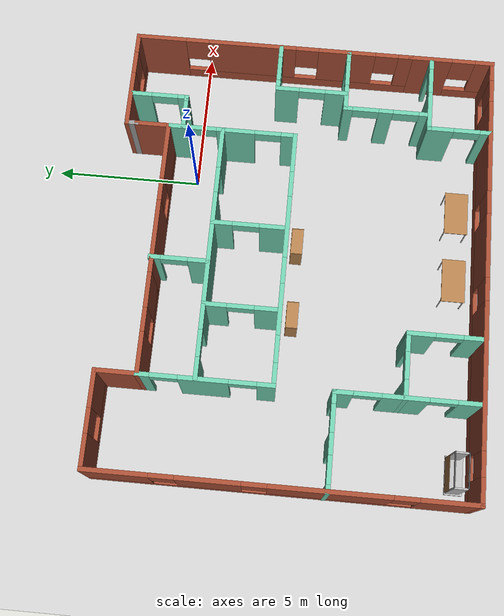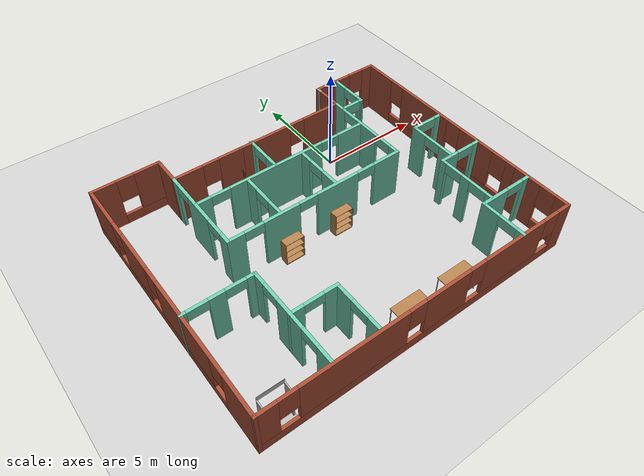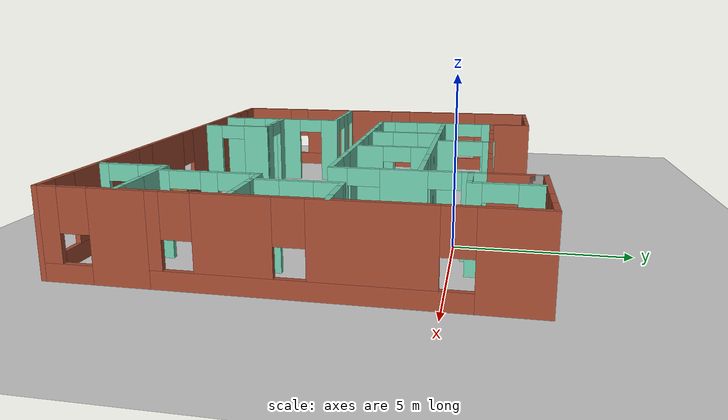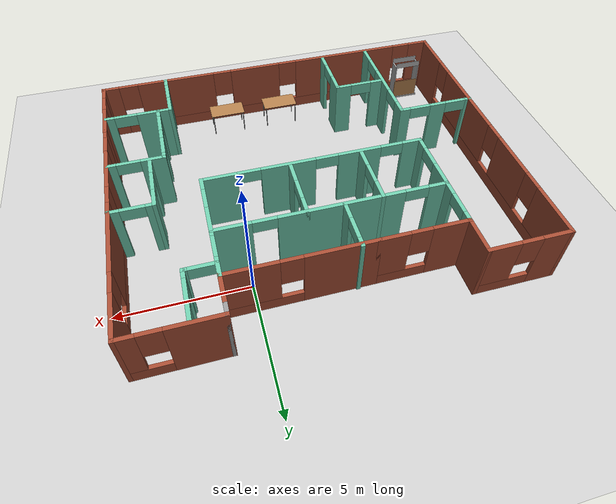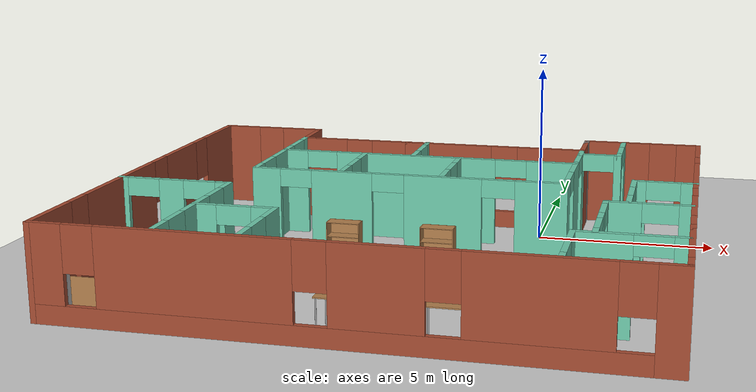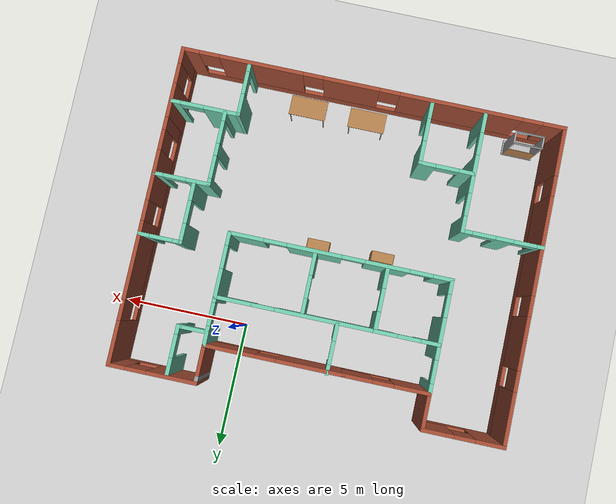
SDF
<sdf version="1.6">
 <world name="default">
  <plugin name="welcome" filename="libwelcome.so"/>
  <light name="sun" type="directional">
   <pose>0 0 10 0 -0 0</pose>
   <diffuse>0.8 0.8 0.8 1</diffuse>
   <specular>0.2 0.2 0.2 1</specular>
   <attenuation>
    <range>1000</range>
    <constant>0.9</constant>
    <linear>0.01</linear>
    <quadratic>0.001</quadratic>
   </attenuation>
   <direction>-0.5 0.1 -0.9</direction>
  </light>
  <model name="ground_plane">
   <static>1</static>
   <link name="link">
    <collision name="collision">
     <geometry><plane><normal>0 0 1</normal><size>100 100</size></plane></geometry>
     <surface>
      <contact><collide_bitmask>65535</collide_bitmask></contact>
      <friction><ode><mu>100</mu><mu2>50</mu2></ode></friction>
     </surface>
    </collision>
    <visual name="visual">
     <cast_shadows>0</cast_shadows>
     <geometry><plane><normal>0 0 1</normal><size>100 100</size></plane></geometry>
     <material>
      <script><uri>file://media/materials/scripts/gazebo.material</uri><name>Gazebo/Grey</name></script>
     </material>
    </visual>
   </link>
  </model>
  <gravity>0 0 -9.8</gravity>
  <magnetic_field>6e-06 2.3e-05 -4.2e-05</magnetic_field>
  <atmosphere type="adiabatic"/>
  <physics name="default_physics" default="0" type="ode">
   <max_step_size>0.001</max_step_size>
   <real_time_factor>1</real_time_factor>
   <real_time_update_rate>1000</real_time_update_rate>
  </physics>
  <scene><ambient>0.4 0.4 0.4 1</ambient><background>0.7 0.7 0.7 1</background><shadows>1</shadows></scene>
  <spherical_coordinates>
   <surface_model>EARTH_WGS84</surface_model>
   <latitude_deg>0</latitude_deg>
   <longitude_deg>0</longitude_deg>
   <elevation>0</elevation>
   <heading_deg>0</heading_deg>
  </spherical_coordinates>
  <model name="my_apartment">
   <pose>-3.10653 -3.79856 0 0 -0 0</pose>
   <link name="Wall_0">
    <pose>1.52918 4.775 0 0 -0 0</pose>
    <visual name="Wall_0_Visual_0">
     <pose>-1.4096 0 1.25 0 -0 0</pose>
     <geometry><box><size>2.6808 0.15 2.5</size></box></geometry>
     <material>
      <script><uri>file://media/materials/scripts/gazebo.material</uri><name>Gazebo/Bricks</name></script>
      <ambient>0.435294 0.796078 0.67451 1</ambient>
     </material>
     <meta><layer>0</layer></meta>
    </visual>
    <collision name="Wall_0_Collision_0">
     <geometry><box><size>2.6808 0.15 2.5</size></box></geometry>
     <pose>-1.4096 0 1.25 0 -0 0</pose>
    </collision>
    <visual name="Wall_0_Visual_1">
     <pose>1.3404 0 0.25 0 -0 0</pose>
     <geometry><box><size>2.8192 0.15 0.5</size></box></geometry>
     <material>
      <script><uri>file://media/materials/scripts/gazebo.material</uri><name>Gazebo/Bricks</name></script>
      <ambient>0.435294 0.796078 0.67451 1</ambient>
     </material>
     <meta><layer>0</layer></meta>
    </visual>
    <collision name="Wall_0_Collision_1">
     <geometry><box><size>2.8192 0.15 0.5</size></box></geometry>
     <pose>1.3404 0 0.25 0 -0 0</pose>
    </collision>
    <visual name="Wall_0_Visual_2">
     <pose>1.7404 0 1.5 0 -0 0</pose>
     <geometry><box><size>2.0192 0.15 2</size></box></geometry>
     <material>
      <script><uri>file://media/materials/scripts/gazebo.material</uri><name>Gazebo/Bricks</name></script>
      <ambient>0.435294 0.796078 0.67451 1</ambient>
     </material>
     <meta><layer>0</layer></meta>
    </visual>
    <collision name="Wall_0_Collision_2">
     <geometry><box><size>2.0192 0.15 2</size></box></geometry>
     <pose>1.7404 0 1.5 0 -0 0</pose>
    </collision>
    <visual name="Wall_0_Visual_3">
     <pose>0.330804 0 1.9 0 -0 0</pose>
     <geometry><box><size>0.8 0.15 1.2</size></box></geometry>
     <material>
      <script><uri>file://media/materials/scripts/gazebo.material</uri><name>Gazebo/Bricks</name></script>
      <ambient>0.435294 0.796078 0.67451 1</ambient>
     </material>
     <meta><layer>0</layer></meta>
    </visual>
    <collision name="Wall_0_Collision_3">
     <geometry><box><size>0.8 0.15 1.2</size></box></geometry>
     <pose>0.330804 0 1.9 0 -0 0</pose>
    </collision>
   </link>
   <link name="Wall_1">
    <collision name="Wall_1_Collision">
     <geometry><box><size>1.25 0.15 2.5</size></box></geometry>
     <pose>0 0 1.25 0 -0 0</pose>
    </collision>
    <visual name="Wall_1_Visual">
     <pose>0 0 1.25 0 -0 0</pose>
     <geometry><box><size>1.25 0.15 2.5</size></box></geometry>
     <material>
      <script><uri>file://media/materials/scripts/gazebo.material</uri><name>Gazebo/Bricks</name></script>
      <ambient>0.435294 0.796078 0.67451 1</ambient>
     </material>
     <meta><layer>0</layer></meta>
    </visual>
    <pose>4.20418 5.325 0 0 -0 1.5708</pose>
   </link>
   <link name="Wall_10">
    <pose>-2.79582 4.775 0 0 -0 0</pose>
    <visual name="Wall_10_Visual_0">
     <pose>-1.0014 0 1.25 0 -0 0</pose>
     <geometry><box><size>1.44721 0.15 2.5</size></box></geometry>
     <material>
      <script><uri>file://media/materials/scripts/gazebo.material</uri><name>Gazebo/Bricks</name></script>
      <ambient>0.435294 0.796078 0.67451 1</ambient>
     </material>
     <meta><layer>0</layer></meta>
    </visual>
    <collision name="Wall_10_Collision_0">
     <geometry><box><size>1.44721 0.15 2.5</size></box></geometry>
     <pose>-1.0014 0 1.25 0 -0 0</pose>
    </collision>
    <visual name="Wall_10_Visual_1">
     <pose>0.723602 0 0.25 0 -0 0</pose>
     <geometry><box><size>2.00279 0.15 0.5</size></box></geometry>
     <material>
      <script><uri>file://media/materials/scripts/gazebo.material</uri><name>Gazebo/Bricks</name></script>
      <ambient>0.435294 0.796078 0.67451 1</ambient>
     </material>
     <meta><layer>0</layer></meta>
    </visual>
    <collision name="Wall_10_Collision_1">
     <geometry><box><size>2.00279 0.15 0.5</size></box></geometry>
     <pose>0.723602 0 0.25 0 -0 0</pose>
    </collision>
    <visual name="Wall_10_Visual_2">
     <pose>1.1236 0 1.5 0 -0 0</pose>
     <geometry><box><size>1.2028 0.15 2</size></box></geometry>
     <material>
      <script><uri>file://media/materials/scripts/gazebo.material</uri><name>Gazebo/Bricks</name></script>
      <ambient>0.435294 0.796078 0.67451 1</ambient>
     </material>
     <meta><layer>0</layer></meta>
    </visual>
    <collision name="Wall_10_Collision_2">
     <geometry><box><size>1.2028 0.15 2</size></box></geometry>
     <pose>1.1236 0 1.5 0 -0 0</pose>
    </collision>
    <visual name="Wall_10_Visual_3">
     <pose>0.122205 0 1.9 0 -0 0</pose>
     <geometry><box><size>0.8 0.15 1.2</size></box></geometry>
     <material>
      <script><uri>file://media/materials/scripts/gazebo.material</uri><name>Gazebo/Bricks</name></script>
      <ambient>0.435294 0.796078 0.67451 1</ambient>
     </material>
     <meta><layer>0</layer></meta>
    </visual>
    <collision name="Wall_10_Collision_3">
     <geometry><box><size>0.8 0.15 1.2</size></box></geometry>
     <pose>0.122205 0 1.9 0 -0 0</pose>
    </collision>
   </link>
   <link name="Wall_12">
    <pose>-4.44565 2.59978 0 0 0 -1.57072</pose>
    <visual name="Wall_12_Visual_0">
     <pose>-2.01587 0 1.25 0 -0 0</pose>
     <geometry><box><size>0.468264 0.15 2.5</size></box></geometry>
     <material>
      <script><uri>file://media/materials/scripts/gazebo.material</uri><name>Gazebo/Grey</name></script>
      <ambient>0.435294 0.796078 0.67451 1</ambient>
     </material>
     <meta><layer>0</layer></meta>
    </visual>
    <collision name="Wall_12_Collision_0">
     <geometry><box><size>0.468264 0.15 2.5</size></box></geometry>
     <pose>-2.01587 0 1.25 0 -0 0</pose>
    </collision>
    <visual name="Wall_12_Visual_1">
     <pose>-0.071119 0 1.25 0 -0 0</pose>
     <geometry><box><size>1.62123 0.15 2.5</size></box></geometry>
     <material>
      <script><uri>file://media/materials/scripts/gazebo.material</uri><name>Gazebo/Grey</name></script>
      <ambient>0.435294 0.796078 0.67451 1</ambient>
     </material>
     <meta><layer>0</layer></meta>
    </visual>
    <collision name="Wall_12_Collision_1">
     <geometry><box><size>1.62123 0.15 2.5</size></box></geometry>
     <pose>-0.071119 0 1.25 0 -0 0</pose>
    </collision>
    <visual name="Wall_12_Visual_2">
     <pose>1.94475 0 1.25 0 -0 0</pose>
     <geometry><box><size>0.610503 0.15 2.5</size></box></geometry>
     <material>
      <script><uri>file://media/materials/scripts/gazebo.material</uri><name>Gazebo/Grey</name></script>
      <ambient>0.435294 0.796078 0.67451 1</ambient>
     </material>
     <meta><layer>0</layer></meta>
    </visual>
    <collision name="Wall_12_Collision_2">
     <geometry><box><size>0.610503 0.15 2.5</size></box></geometry>
     <pose>1.94475 0 1.25 0 -0 0</pose>
    </collision>
    <visual name="Wall_12_Visual_3">
     <pose>-1.33174 0 2.25 0 -0 0</pose>
     <geometry><box><size>0.9 0.15 0.5</size></box></geometry>
     <material>
      <script><uri>file://media/materials/scripts/gazebo.material</uri><name>Gazebo/Grey</name></script>
      <ambient>0.435294 0.796078 0.67451 1</ambient>
     </material>
     <meta><layer>0</layer></meta>
    </visual>
    <collision name="Wall_12_Collision_3">
     <geometry><box><size>0.9 0.15 0.5</size></box></geometry>
     <pose>-1.33174 0 2.25 0 -0 0</pose>
    </collision>
    <visual name="Wall_12_Visual_4">
     <pose>1.1895 0 2.25 0 -0 0</pose>
     <geometry><box><size>0.9 0.15 0.5</size></box></geometry>
     <material>
      <script><uri>file://media/materials/scripts/gazebo.material</uri><name>Gazebo/Grey</name></script>
      <ambient>0.435294 0.796078 0.67451 1</ambient>
     </material>
     <meta><layer>0</layer></meta>
    </visual>
    <collision name="Wall_12_Collision_4">
     <geometry><box><size>0.9 0.15 0.5</size></box></geometry>
     <pose>1.1895 0 2.25 0 -0 0</pose>
    </collision>
   </link>
   <link name="Wall_13">
    <pose>-0.120473 0.424565 0 0 -0 0</pose>
    <visual name="Wall_13_Visual_0">
     <pose>-3.99093 0 1.25 0 -0 0</pose>
     <geometry><box><size>0.818142 0.15 2.5</size></box></geometry>
     <material>
      <script><uri>file://media/materials/scripts/gazebo.material</uri><name>Gazebo/Grey</name></script>
      <ambient>0.435294 0.796078 0.67451 1</ambient>
     </material>
     <meta><layer>0</layer></meta>
    </visual>
    <collision name="Wall_13_Collision_0">
     <geometry><box><size>0.818142 0.15 2.5</size></box></geometry>
     <pose>-3.99093 0 1.25 0 -0 0</pose>
    </collision>
    <visual name="Wall_13_Visual_1">
     <pose>-1.8163 0 1.25 0 -0 0</pose>
     <geometry><box><size>1.73111 0.15 2.5</size></box></geometry>
     <material>
      <script><uri>file://media/materials/scripts/gazebo.material</uri><name>Gazebo/Grey</name></script>
      <ambient>0.435294 0.796078 0.67451 1</ambient>
     </material>
     <meta><layer>0</layer></meta>
    </visual>
    <collision name="Wall_13_Collision_1">
     <geometry><box><size>1.73111 0.15 2.5</size></box></geometry>
     <pose>-1.8163 0 1.25 0 -0 0</pose>
    </collision>
    <visual name="Wall_13_Visual_2">
     <pose>1.02013 0 1.25 0 -0 0</pose>
     <geometry><box><size>2.14175 0.15 2.5</size></box></geometry>
     <material>
      <script><uri>file://media/materials/scripts/gazebo.material</uri><name>Gazebo/Grey</name></script>
      <ambient>0.435294 0.796078 0.67451 1</ambient>
     </material>
     <meta><layer>0</layer></meta>
    </visual>
    <collision name="Wall_13_Collision_2">
     <geometry><box><size>2.14175 0.15 2.5</size></box></geometry>
     <pose>1.02013 0 1.25 0 -0 0</pose>
    </collision>
    <visual name="Wall_13_Visual_3">
     <pose>3.6955 0 1.25 0 -0 0</pose>
     <geometry><box><size>1.40899 0.15 2.5</size></box></geometry>
     <material>
      <script><uri>file://media/materials/scripts/gazebo.material</uri><name>Gazebo/Grey</name></script>
      <ambient>0.435294 0.796078 0.67451 1</ambient>
     </material>
     <meta><layer>0</layer></meta>
    </visual>
    <collision name="Wall_13_Collision_3">
     <geometry><box><size>1.40899 0.15 2.5</size></box></geometry>
     <pose>3.6955 0 1.25 0 -0 0</pose>
    </collision>
    <visual name="Wall_13_Visual_4">
     <pose>-3.13186 0 2.25 0 -0 0</pose>
     <geometry><box><size>0.9 0.15 0.5</size></box></geometry>
     <material>
      <script><uri>file://media/materials/scripts/gazebo.material</uri><name>Gazebo/Grey</name></script>
      <ambient>0.435294 0.796078 0.67451 1</ambient>
     </material>
     <meta><layer>0</layer></meta>
    </visual>
    <collision name="Wall_13_Collision_4">
     <geometry><box><size>0.9 0.15 0.5</size></box></geometry>
     <pose>-3.13186 0 2.25 0 -0 0</pose>
    </collision>
    <visual name="Wall_13_Visual_5">
     <pose>-0.500745 0 2.25 0 -0 0</pose>
     <geometry><box><size>0.9 0.15 0.5</size></box></geometry>
     <material>
      <script><uri>file://media/materials/scripts/gazebo.material</uri><name>Gazebo/Grey</name></script>
      <ambient>0.435294 0.796078 0.67451 1</ambient>
     </material>
     <meta><layer>0</layer></meta>
    </visual>
    <collision name="Wall_13_Collision_5">
     <geometry><box><size>0.9 0.15 0.5</size></box></geometry>
     <pose>-0.500745 0 2.25 0 -0 0</pose>
    </collision>
    <visual name="Wall_13_Visual_6">
     <pose>2.54101 0 2.25 0 -0 0</pose>
     <geometry><box><size>0.9 0.15 0.5</size></box></geometry>
     <material>
      <script><uri>file://media/materials/scripts/gazebo.material</uri><name>Gazebo/Grey</name></script>
      <ambient>0.435294 0.796078 0.67451 1</ambient>
     </material>
     <meta><layer>0</layer></meta>
    </visual>
    <collision name="Wall_13_Collision_6">
     <geometry><box><size>0.9 0.15 0.5</size></box></geometry>
     <pose>2.54101 0 2.25 0 -0 0</pose>
    </collision>
   </link>
   <link name="Wall_17">
    <pose>4.20435 2.59978 0 0 -0 1.57088</pose>
    <visual name="Wall_17_Visual_0">
     <pose>-1.96795 0 1.25 0 -0 0</pose>
     <geometry><box><size>0.564378 0.15 2.5</size></box></geometry>
     <material>
      <script><uri>file://media/materials/scripts/gazebo.material</uri><name>Gazebo/Grey</name></script>
      <ambient>0.435294 0.796078 0.67451 1</ambient>
     </material>
     <meta><layer>0</layer></meta>
    </visual>
    <collision name="Wall_17_Collision_0">
     <geometry><box><size>0.564378 0.15 2.5</size></box></geometry>
     <pose>-1.96795 0 1.25 0 -0 0</pose>
    </collision>
    <visual name="Wall_17_Visual_1">
     <pose>-0.125495 0 1.25 0 -0 0</pose>
     <geometry><box><size>1.32054 0.15 2.5</size></box></geometry>
     <material>
      <script><uri>file://media/materials/scripts/gazebo.material</uri><name>Gazebo/Grey</name></script>
      <ambient>0.435294 0.796078 0.67451 1</ambient>
     </material>
     <meta><layer>0</layer></meta>
    </visual>
    <collision name="Wall_17_Collision_1">
     <geometry><box><size>1.32054 0.15 2.5</size></box></geometry>
     <pose>-0.125495 0 1.25 0 -0 0</pose>
    </collision>
    <visual name="Wall_17_Visual_2">
     <pose>1.84246 0 1.25 0 -0 0</pose>
     <geometry><box><size>0.815367 0.15 2.5</size></box></geometry>
     <material>
      <script><uri>file://media/materials/scripts/gazebo.material</uri><name>Gazebo/Grey</name></script>
      <ambient>0.435294 0.796078 0.67451 1</ambient>
     </material>
     <meta><layer>0</layer></meta>
    </visual>
    <collision name="Wall_17_Collision_2">
     <geometry><box><size>0.815367 0.15 2.5</size></box></geometry>
     <pose>1.84246 0 1.25 0 -0 0</pose>
    </collision>
    <visual name="Wall_17_Visual_3">
     <pose>-1.23577 0 2.25 0 -0 0</pose>
     <geometry><box><size>0.9 0.15 0.5</size></box></geometry>
     <material>
      <script><uri>file://media/materials/scripts/gazebo.material</uri><name>Gazebo/Grey</name></script>
      <ambient>0.435294 0.796078 0.67451 1</ambient>
     </material>
     <meta><layer>0</layer></meta>
    </visual>
    <collision name="Wall_17_Collision_3">
     <geometry><box><size>0.9 0.15 0.5</size></box></geometry>
     <pose>-1.23577 0 2.25 0 -0 0</pose>
    </collision>
    <visual name="Wall_17_Visual_4">
     <pose>0.984776 0 2.25 0 -0 0</pose>
     <geometry><box><size>0.9 0.15 0.5</size></box></geometry>
     <material>
      <script><uri>file://media/materials/scripts/gazebo.material</uri><name>Gazebo/Grey</name></script>
      <ambient>0.435294 0.796078 0.67451 1</ambient>
     </material>
     <meta><layer>0</layer></meta>
    </visual>
    <collision name="Wall_17_Collision_4">
     <geometry><box><size>0.9 0.15 0.5</size></box></geometry>
     <pose>0.984776 0 2.25 0 -0 0</pose>
    </collision>
   </link>
   <link name="Wall_19">
    <pose>-0.118146 2.91521 0 0 -0 0</pose>
    <visual name="Wall_19_Visual_0">
     <pose>-3.9948 0 1.25 0 -0 0</pose>
     <geometry><box><size>0.760398 0.15 2.5</size></box></geometry>
     <material>
      <script><uri>file://media/materials/scripts/gazebo.material</uri><name>Gazebo/Grey</name></script>
      <ambient>0.435294 0.796078 0.67451 1</ambient>
     </material>
     <meta><layer>0</layer></meta>
    </visual>
    <collision name="Wall_19_Collision_0">
     <geometry><box><size>0.760398 0.15 2.5</size></box></geometry>
     <pose>-3.9948 0 1.25 0 -0 0</pose>
    </collision>
    <visual name="Wall_19_Visual_1">
     <pose>-0.343379 0 1.25 0 -0 0</pose>
     <geometry><box><size>4.74245 0.15 2.5</size></box></geometry>
     <material>
      <script><uri>file://media/materials/scripts/gazebo.material</uri><name>Gazebo/Grey</name></script>
      <ambient>0.435294 0.796078 0.67451 1</ambient>
     </material>
     <meta><layer>0</layer></meta>
    </visual>
    <collision name="Wall_19_Collision_1">
     <geometry><box><size>4.74245 0.15 2.5</size></box></geometry>
     <pose>-0.343379 0 1.25 0 -0 0</pose>
    </collision>
    <visual name="Wall_19_Visual_2">
     <pose>3.65142 0 1.25 0 -0 0</pose>
     <geometry><box><size>1.44716 0.15 2.5</size></box></geometry>
     <material>
      <script><uri>file://media/materials/scripts/gazebo.material</uri><name>Gazebo/Grey</name></script>
      <ambient>0.435294 0.796078 0.67451 1</ambient>
     </material>
     <meta><layer>0</layer></meta>
    </visual>
    <collision name="Wall_19_Collision_2">
     <geometry><box><size>1.44716 0.15 2.5</size></box></geometry>
     <pose>3.65142 0 1.25 0 -0 0</pose>
    </collision>
    <visual name="Wall_19_Visual_3">
     <pose>-3.1646 0 2.25 0 -0 0</pose>
     <geometry><box><size>0.9 0.15 0.5</size></box></geometry>
     <material>
      <script><uri>file://media/materials/scripts/gazebo.material</uri><name>Gazebo/Grey</name></script>
      <ambient>0.435294 0.796078 0.67451 1</ambient>
     </material>
     <meta><layer>0</layer></meta>
    </visual>
    <collision name="Wall_19_Collision_3">
     <geometry><box><size>0.9 0.15 0.5</size></box></geometry>
     <pose>-3.1646 0 2.25 0 -0 0</pose>
    </collision>
    <visual name="Wall_19_Visual_4">
     <pose>2.47784 0 2.25 0 -0 0</pose>
     <geometry><box><size>0.9 0.15 0.5</size></box></geometry>
     <material>
      <script><uri>file://media/materials/scripts/gazebo.material</uri><name>Gazebo/Grey</name></script>
      <ambient>0.435294 0.796078 0.67451 1</ambient>
     </material>
     <meta><layer>0</layer></meta>
    </visual>
    <collision name="Wall_19_Collision_4">
     <geometry><box><size>0.9 0.15 0.5</size></box></geometry>
     <pose>2.47784 0 2.25 0 -0 0</pose>
    </collision>
   </link>
   <link name="Wall_2">
    <collision name="Wall_2_Collision">
     <geometry><box><size>0.5 0.15 2.5</size></box></geometry>
     <pose>0 0 1.25 0 -0 0</pose>
    </collision>
    <visual name="Wall_2_Visual">
     <pose>0 0 1.25 0 -0 0</pose>
     <geometry><box><size>0.5 0.15 2.5</size></box></geometry>
     <material>
      <script><uri>file://media/materials/scripts/gazebo.material</uri><name>Gazebo/Grey</name></script>
      <ambient>1 1 1 1</ambient>
     </material>
     <meta><layer>0</layer></meta>
    </visual>
    <pose>4.20418 6.05 0 0 -0 1.5708</pose>
   </link>
   <link name="Wall_21">
    <pose>-1.97093 1.74021 0 0 0 -1.5708</pose>
    <visual name="Wall_21_Visual_0">
     <pose>-0.835388 0 1.25 0 -0 0</pose>
     <geometry><box><size>0.829225 0.15 2.5</size></box></geometry>
     <material>
      <script><uri>file://media/materials/scripts/gazebo.material</uri><name>Gazebo/Grey</name></script>
      <ambient>0.435294 0.796078 0.67451 1</ambient>
     </material>
     <meta><layer>0</layer></meta>
    </visual>
    <collision name="Wall_21_Collision_0">
     <geometry><box><size>0.829225 0.15 2.5</size></box></geometry>
     <pose>-0.835388 0 1.25 0 -0 0</pose>
    </collision>
    <visual name="Wall_21_Visual_1">
     <pose>0.864612 0 1.25 0 -0 0</pose>
     <geometry><box><size>0.770775 0.15 2.5</size></box></geometry>
     <material>
      <script><uri>file://media/materials/scripts/gazebo.material</uri><name>Gazebo/Grey</name></script>
      <ambient>0.435294 0.796078 0.67451 1</ambient>
     </material>
     <meta><layer>0</layer></meta>
    </visual>
    <collision name="Wall_21_Collision_1">
     <geometry><box><size>0.770775 0.15 2.5</size></box></geometry>
     <pose>0.864612 0 1.25 0 -0 0</pose>
    </collision>
    <visual name="Wall_21_Visual_2">
     <pose>0.029225 0 2.25 0 -0 0</pose>
     <geometry><box><size>0.9 0.15 0.5</size></box></geometry>
     <material>
      <script><uri>file://media/materials/scripts/gazebo.material</uri><name>Gazebo/Grey</name></script>
      <ambient>0.435294 0.796078 0.67451 1</ambient>
     </material>
     <meta><layer>0</layer></meta>
    </visual>
    <collision name="Wall_21_Collision_2">
     <geometry><box><size>0.9 0.15 0.5</size></box></geometry>
     <pose>0.029225 0 2.25 0 -0 0</pose>
    </collision>
   </link>
   <link name="Wall_23">
    <pose>0.843373 1.74021 0 0 0 -1.5708</pose>
    <visual name="Wall_23_Visual_0">
     <pose>-0.881649 0 1.25 0 -0 0</pose>
     <geometry><box><size>0.736702 0.15 2.5</size></box></geometry>
     <material>
      <script><uri>file://media/materials/scripts/gazebo.material</uri><name>Gazebo/Grey</name></script>
      <ambient>0.435294 0.796078 0.67451 1</ambient>
     </material>
     <meta><layer>0</layer></meta>
    </visual>
    <collision name="Wall_23_Collision_0">
     <geometry><box><size>0.736702 0.15 2.5</size></box></geometry>
     <pose>-0.881649 0 1.25 0 -0 0</pose>
    </collision>
    <visual name="Wall_23_Visual_1">
     <pose>0.818351 0 1.25 0 -0 0</pose>
     <geometry><box><size>0.863298 0.15 2.5</size></box></geometry>
     <material>
      <script><uri>file://media/materials/scripts/gazebo.material</uri><name>Gazebo/Grey</name></script>
      <ambient>0.435294 0.796078 0.67451 1</ambient>
     </material>
     <meta><layer>0</layer></meta>
    </visual>
    <collision name="Wall_23_Collision_1">
     <geometry><box><size>0.863298 0.15 2.5</size></box></geometry>
     <pose>0.818351 0 1.25 0 -0 0</pose>
    </collision>
    <visual name="Wall_23_Visual_2">
     <pose>-0.063298 0 2.25 0 -0 0</pose>
     <geometry><box><size>0.9 0.15 0.5</size></box></geometry>
     <material>
      <script><uri>file://media/materials/scripts/gazebo.material</uri><name>Gazebo/Grey</name></script>
      <ambient>0.435294 0.796078 0.67451 1</ambient>
     </material>
     <meta><layer>0</layer></meta>
    </visual>
    <collision name="Wall_23_Collision_2">
     <geometry><box><size>0.9 0.15 0.5</size></box></geometry>
     <pose>-0.063298 0 2.25 0 -0 0</pose>
    </collision>
   </link>
   <link name="Wall_25">
    <pose>-0.533187 3.90139 0 0 -0 1.5708</pose>
    <visual name="Wall_25_Visual_0">
     <pose>-0.652107 0 1.25 0 -0 0</pose>
     <geometry><box><size>0.695786 0.15 2.5</size></box></geometry>
     <material>
      <script><uri>file://media/materials/scripts/gazebo.material</uri><name>Gazebo/Grey</name></script>
      <ambient>0.435294 0.796078 0.67451 1</ambient>
     </material>
     <meta><layer>0</layer></meta>
    </visual>
    <collision name="Wall_25_Collision_0">
     <geometry><box><size>0.695786 0.15 2.5</size></box></geometry>
     <pose>-0.652107 0 1.25 0 -0 0</pose>
    </collision>
    <visual name="Wall_25_Visual_1">
     <pose>0.797893 0 1.25 0 -0 0</pose>
     <geometry><box><size>0.404214 0.15 2.5</size></box></geometry>
     <material>
      <script><uri>file://media/materials/scripts/gazebo.material</uri><name>Gazebo/Grey</name></script>
      <ambient>0.435294 0.796078 0.67451 1</ambient>
     </material>
     <meta><layer>0</layer></meta>
    </visual>
    <collision name="Wall_25_Collision_1">
     <geometry><box><size>0.404214 0.15 2.5</size></box></geometry>
     <pose>0.797893 0 1.25 0 -0 0</pose>
    </collision>
    <visual name="Wall_25_Visual_2">
     <pose>0.145786 0 2.25 0 -0 0</pose>
     <geometry><box><size>0.9 0.15 0.5</size></box></geometry>
     <material>
      <script><uri>file://media/materials/scripts/gazebo.material</uri><name>Gazebo/Grey</name></script>
      <ambient>0.435294 0.796078 0.67451 1</ambient>
     </material>
     <meta><layer>0</layer></meta>
    </visual>
    <collision name="Wall_25_Collision_2">
     <geometry><box><size>0.9 0.15 0.5</size></box></geometry>
     <pose>0.145786 0 2.25 0 -0 0</pose>
    </collision>
   </link>
   <link name="Wall_27">
    <pose>4.7693 4.27848 0 0 -0 0</pose>
    <visual name="Wall_27_Visual_0">
     <pose>-0.558063 0 1.25 0 -0 0</pose>
     <geometry><box><size>0.133873 0.15 2.5</size></box></geometry>
     <material>
      <script><uri>file://media/materials/scripts/gazebo.material</uri><name>Gazebo/Grey</name></script>
      <ambient>0.435294 0.796078 0.67451 1</ambient>
     </material>
     <meta><layer>0</layer></meta>
    </visual>
    <collision name="Wall_27_Collision_0">
     <geometry><box><size>0.133873 0.15 2.5</size></box></geometry>
     <pose>-0.558063 0 1.25 0 -0 0</pose>
    </collision>
    <visual name="Wall_27_Visual_1">
     <pose>0.516937 0 1.25 0 -0 0</pose>
     <geometry><box><size>0.216127 0.15 2.5</size></box></geometry>
     <material>
      <script><uri>file://media/materials/scripts/gazebo.material</uri><name>Gazebo/Grey</name></script>
      <ambient>0.435294 0.796078 0.67451 1</ambient>
     </material>
     <meta><layer>0</layer></meta>
    </visual>
    <collision name="Wall_27_Collision_1">
     <geometry><box><size>0.216127 0.15 2.5</size></box></geometry>
     <pose>0.516937 0 1.25 0 -0 0</pose>
    </collision>
    <visual name="Wall_27_Visual_2">
     <pose>-0.041127 0 2.25 0 -0 0</pose>
     <geometry><box><size>0.9 0.15 0.5</size></box></geometry>
     <material>
      <script><uri>file://media/materials/scripts/gazebo.material</uri><name>Gazebo/Grey</name></script>
      <ambient>0.435294 0.796078 0.67451 1</ambient>
     </material>
     <meta><layer>0</layer></meta>
    </visual>
    <collision name="Wall_27_Collision_2">
     <geometry><box><size>0.9 0.15 0.5</size></box></geometry>
     <pose>-0.041127 0 2.25 0 -0 0</pose>
    </collision>
   </link>
   <link name="Wall_28">
    <pose>5.3193 5.20348 0 0 -0 1.5708</pose>
    <visual name="Wall_28_Visual_0">
     <pose>-0.805845 0 1.25 0 -0 0</pose>
     <geometry><box><size>0.38831 0.15 2.5</size></box></geometry>
     <material>
      <script><uri>file://media/materials/scripts/gazebo.material</uri><name>Gazebo/Grey</name></script>
      <ambient>0.435294 0.796078 0.67451 1</ambient>
     </material>
     <meta><layer>0</layer></meta>
    </visual>
    <collision name="Wall_28_Collision_0">
     <geometry><box><size>0.38831 0.15 2.5</size></box></geometry>
     <pose>-0.805845 0 1.25 0 -0 0</pose>
    </collision>
    <visual name="Wall_28_Visual_1">
     <pose>0.644155 0 1.25 0 -0 0</pose>
     <geometry><box><size>0.71169 0.15 2.5</size></box></geometry>
     <material>
      <script><uri>file://media/materials/scripts/gazebo.material</uri><name>Gazebo/Grey</name></script>
      <ambient>0.435294 0.796078 0.67451 1</ambient>
     </material>
     <meta><layer>0</layer></meta>
    </visual>
    <collision name="Wall_28_Collision_1">
     <geometry><box><size>0.71169 0.15 2.5</size></box></geometry>
     <pose>0.644155 0 1.25 0 -0 0</pose>
    </collision>
    <visual name="Wall_28_Visual_2">
     <pose>-0.16169 0 2.25 0 -0 0</pose>
     <geometry><box><size>0.9 0.15 0.5</size></box></geometry>
     <material>
      <script><uri>file://media/materials/scripts/gazebo.material</uri><name>Gazebo/Grey</name></script>
      <ambient>0.435294 0.796078 0.67451 1</ambient>
     </material>
     <meta><layer>0</layer></meta>
    </visual>
    <collision name="Wall_28_Collision_2">
     <geometry><box><size>0.9 0.15 0.5</size></box></geometry>
     <pose>-0.16169 0 2.25 0 -0 0</pose>
    </collision>
   </link>
   <link name="Wall_3">
    <pose>5.87918 6.225 0 0 -0 0</pose>
    <visual name="Wall_3_Visual_0">
     <pose>-0.759972 0 1.25 0 -0 0</pose>
     <geometry><box><size>1.98006 0.15 2.5</size></box></geometry>
     <material>
      <script><uri>file://media/materials/scripts/gazebo.material</uri><name>Gazebo/Bricks</name></script>
      <ambient>0.435294 0.796078 0.67451 1</ambient>
     </material>
     <meta><layer>0</layer></meta>
    </visual>
    <collision name="Wall_3_Collision_0">
     <geometry><box><size>1.98006 0.15 2.5</size></box></geometry>
     <pose>-0.759972 0 1.25 0 -0 0</pose>
    </collision>
    <visual name="Wall_3_Visual_1">
     <pose>0.990028 0 0.25 0 -0 0</pose>
     <geometry><box><size>1.51994 0.15 0.5</size></box></geometry>
     <material>
      <script><uri>file://media/materials/scripts/gazebo.material</uri><name>Gazebo/Bricks</name></script>
      <ambient>0.435294 0.796078 0.67451 1</ambient>
     </material>
     <meta><layer>0</layer></meta>
    </visual>
    <collision name="Wall_3_Collision_1">
     <geometry><box><size>1.51994 0.15 0.5</size></box></geometry>
     <pose>0.990028 0 0.25 0 -0 0</pose>
    </collision>
    <visual name="Wall_3_Visual_2">
     <pose>1.39003 0 1.5 0 -0 0</pose>
     <geometry><box><size>0.719944 0.15 2</size></box></geometry>
     <material>
      <script><uri>file://media/materials/scripts/gazebo.material</uri><name>Gazebo/Bricks</name></script>
      <ambient>0.435294 0.796078 0.67451 1</ambient>
     </material>
     <meta><layer>0</layer></meta>
    </visual>
    <collision name="Wall_3_Collision_2">
     <geometry><box><size>0.719944 0.15 2</size></box></geometry>
     <pose>1.39003 0 1.5 0 -0 0</pose>
    </collision>
    <visual name="Wall_3_Visual_3">
     <pose>0.630056 0 1.9 0 -0 0</pose>
     <geometry><box><size>0.8 0.15 1.2</size></box></geometry>
     <material>
      <script><uri>file://media/materials/scripts/gazebo.material</uri><name>Gazebo/Bricks</name></script>
      <ambient>0.435294 0.796078 0.67451 1</ambient>
     </material>
     <meta><layer>0</layer></meta>
    </visual>
    <collision name="Wall_3_Collision_3">
     <geometry><box><size>0.8 0.15 1.2</size></box></geometry>
     <pose>0.630056 0 1.9 0 -0 0</pose>
    </collision>
   </link>
   <link name="Wall_30">
    <pose>4.89009 -5.17282 0 0 -0 1.5708</pose>
    <visual name="Wall_30_Visual_0">
     <pose>-0.907714 0 1.25 0 -0 0</pose>
     <geometry><box><size>0.434571 0.15 2.5</size></box></geometry>
     <material>
      <script><uri>file://media/materials/scripts/gazebo.material</uri><name>Gazebo/Grey</name></script>
      <ambient>0.435294 0.796078 0.67451 1</ambient>
     </material>
     <meta><layer>0</layer></meta>
    </visual>
    <collision name="Wall_30_Collision_0">
     <geometry><box><size>0.434571 0.15 2.5</size></box></geometry>
     <pose>-0.907714 0 1.25 0 -0 0</pose>
    </collision>
    <visual name="Wall_30_Visual_1">
     <pose>0.667286 0 1.25 0 -0 0</pose>
     <geometry><box><size>0.915429 0.15 2.5</size></box></geometry>
     <material>
      <script><uri>file://media/materials/scripts/gazebo.material</uri><name>Gazebo/Grey</name></script>
      <ambient>0.435294 0.796078 0.67451 1</ambient>
     </material>
     <meta><layer>0</layer></meta>
    </visual>
    <collision name="Wall_30_Collision_1">
     <geometry><box><size>0.915429 0.15 2.5</size></box></geometry>
     <pose>0.667286 0 1.25 0 -0 0</pose>
    </collision>
    <visual name="Wall_30_Visual_2">
     <pose>-0.240429 0 2.25 0 -0 0</pose>
     <geometry><box><size>0.9 0.15 0.5</size></box></geometry>
     <material>
      <script><uri>file://media/materials/scripts/gazebo.material</uri><name>Gazebo/Grey</name></script>
      <ambient>0.435294 0.796078 0.67451 1</ambient>
     </material>
     <meta><layer>0</layer></meta>
    </visual>
    <collision name="Wall_30_Collision_2">
     <geometry><box><size>0.9 0.15 0.5</size></box></geometry>
     <pose>-0.240429 0 2.25 0 -0 0</pose>
    </collision>
   </link>
   <link name="Wall_31">
    <pose>6.19009 -4.12282 0 0 -0 0</pose>
    <visual name="Wall_31_Visual_0">
     <pose>-0.648841 0 1.25 0 -0 0</pose>
     <geometry><box><size>1.45232 0.15 2.5</size></box></geometry>
     <material>
      <script><uri>file://media/materials/scripts/gazebo.material</uri><name>Gazebo/Grey</name></script>
      <ambient>0.435294 0.796078 0.67451 1</ambient>
     </material>
     <meta><layer>0</layer></meta>
    </visual>
    <collision name="Wall_31_Collision_0">
     <geometry><box><size>1.45232 0.15 2.5</size></box></geometry>
     <pose>-0.648841 0 1.25 0 -0 0</pose>
    </collision>
    <visual name="Wall_31_Visual_1">
     <pose>1.17616 0 1.25 0 -0 0</pose>
     <geometry><box><size>0.397682 0.15 2.5</size></box></geometry>
     <material>
      <script><uri>file://media/materials/scripts/gazebo.material</uri><name>Gazebo/Grey</name></script>
      <ambient>0.435294 0.796078 0.67451 1</ambient>
     </material>
     <meta><layer>0</layer></meta>
    </visual>
    <collision name="Wall_31_Collision_1">
     <geometry><box><size>0.397682 0.15 2.5</size></box></geometry>
     <pose>1.17616 0 1.25 0 -0 0</pose>
    </collision>
    <visual name="Wall_31_Visual_2">
     <pose>0.527318 0 2.25 0 -0 0</pose>
     <geometry><box><size>0.9 0.15 0.5</size></box></geometry>
     <material>
      <script><uri>file://media/materials/scripts/gazebo.material</uri><name>Gazebo/Grey</name></script>
      <ambient>0.435294 0.796078 0.67451 1</ambient>
     </material>
     <meta><layer>0</layer></meta>
    </visual>
    <collision name="Wall_31_Collision_2">
     <geometry><box><size>0.9 0.15 0.5</size></box></geometry>
     <pose>0.527318 0 2.25 0 -0 0</pose>
    </collision>
   </link>
   <link name="Wall_33">
    <pose>5.39896 -2.64667 0 0 -0 1.5708</pose>
    <visual name="Wall_33_Visual_0">
     <pose>-1.30584 0 1.25 0 -0 0</pose>
     <geometry><box><size>0.38831 0.15 2.5</size></box></geometry>
     <material>
      <script><uri>file://media/materials/scripts/gazebo.material</uri><name>Gazebo/Grey</name></script>
      <ambient>0.435294 0.796078 0.67451 1</ambient>
     </material>
     <meta><layer>0</layer></meta>
    </visual>
    <collision name="Wall_33_Collision_0">
     <geometry><box><size>0.38831 0.15 2.5</size></box></geometry>
     <pose>-1.30584 0 1.25 0 -0 0</pose>
    </collision>
    <visual name="Wall_33_Visual_1">
     <pose>0.032228 0 1.25 0 -0 0</pose>
     <geometry><box><size>0.487836 0.15 2.5</size></box></geometry>
     <material>
      <script><uri>file://media/materials/scripts/gazebo.material</uri><name>Gazebo/Grey</name></script>
      <ambient>0.435294 0.796078 0.67451 1</ambient>
     </material>
     <meta><layer>0</layer></meta>
    </visual>
    <collision name="Wall_33_Collision_1">
     <geometry><box><size>0.487836 0.15 2.5</size></box></geometry>
     <pose>0.032228 0 1.25 0 -0 0</pose>
    </collision>
    <visual name="Wall_33_Visual_2">
     <pose>1.33807 0 1.25 0 -0 0</pose>
     <geometry><box><size>0.323854 0.15 2.5</size></box></geometry>
     <material>
      <script><uri>file://media/materials/scripts/gazebo.material</uri><name>Gazebo/Grey</name></script>
      <ambient>0.435294 0.796078 0.67451 1</ambient>
     </material>
     <meta><layer>0</layer></meta>
    </visual>
    <collision name="Wall_33_Collision_2">
     <geometry><box><size>0.323854 0.15 2.5</size></box></geometry>
     <pose>1.33807 0 1.25 0 -0 0</pose>
    </collision>
    <visual name="Wall_33_Visual_3">
     <pose>-0.66169 0 2.25 0 -0 0</pose>
     <geometry><box><size>0.9 0.15 0.5</size></box></geometry>
     <material>
      <script><uri>file://media/materials/scripts/gazebo.material</uri><name>Gazebo/Grey</name></script>
      <ambient>0.435294 0.796078 0.67451 1</ambient>
     </material>
     <meta><layer>0</layer></meta>
    </visual>
    <collision name="Wall_33_Collision_3">
     <geometry><box><size>0.9 0.15 0.5</size></box></geometry>
     <pose>-0.66169 0 2.25 0 -0 0</pose>
    </collision>
    <visual name="Wall_33_Visual_4">
     <pose>0.726146 0 2.25 0 -0 0</pose>
     <geometry><box><size>0.9 0.15 0.5</size></box></geometry>
     <material>
      <script><uri>file://media/materials/scripts/gazebo.material</uri><name>Gazebo/Grey</name></script>
      <ambient>0.435294 0.796078 0.67451 1</ambient>
     </material>
     <meta><layer>0</layer></meta>
    </visual>
    <collision name="Wall_33_Collision_4">
     <geometry><box><size>0.9 0.15 0.5</size></box></geometry>
     <pose>0.726146 0 2.25 0 -0 0</pose>
    </collision>
   </link>
   <link name="Wall_34">
    <pose>6.44896 -1.22167 0 0 -0 0</pose>
    <visual name="Wall_34_Visual_0">
     <pose>-0.641712 0 1.25 0 -0 0</pose>
     <geometry><box><size>0.966575 0.15 2.5</size></box></geometry>
     <material>
      <script><uri>file://media/materials/scripts/gazebo.material</uri><name>Gazebo/Grey</name></script>
      <ambient>0.435294 0.796078 0.67451 1</ambient>
     </material>
     <meta><layer>0</layer></meta>
    </visual>
    <collision name="Wall_34_Collision_0">
     <geometry><box><size>0.966575 0.15 2.5</size></box></geometry>
     <pose>-0.641712 0 1.25 0 -0 0</pose>
    </collision>
    <visual name="Wall_34_Visual_1">
     <pose>0.933288 0 1.25 0 -0 0</pose>
     <geometry><box><size>0.383425 0.15 2.5</size></box></geometry>
     <material>
      <script><uri>file://media/materials/scripts/gazebo.material</uri><name>Gazebo/Grey</name></script>
      <ambient>0.435294 0.796078 0.67451 1</ambient>
     </material>
     <meta><layer>0</layer></meta>
    </visual>
    <collision name="Wall_34_Collision_1">
     <geometry><box><size>0.383425 0.15 2.5</size></box></geometry>
     <pose>0.933288 0 1.25 0 -0 0</pose>
    </collision>
    <visual name="Wall_34_Visual_2">
     <pose>0.291575 0 2.25 0 -0 0</pose>
     <geometry><box><size>0.9 0.15 0.5</size></box></geometry>
     <material>
      <script><uri>file://media/materials/scripts/gazebo.material</uri><name>Gazebo/Grey</name></script>
      <ambient>0.435294 0.796078 0.67451 1</ambient>
     </material>
     <meta><layer>0</layer></meta>
    </visual>
    <collision name="Wall_34_Collision_2">
     <geometry><box><size>0.9 0.15 0.5</size></box></geometry>
     <pose>0.291575 0 2.25 0 -0 0</pose>
    </collision>
   </link>
   <link name="Wall_36">
    <pose>5.9541 -0.005345 0 0 -0 1.5708</pose>
    <visual name="Wall_36_Visual_0">
     <pose>-0.859235 0 1.25 0 -0 0</pose>
     <geometry><box><size>0.78153 0.15 2.5</size></box></geometry>
     <material>
      <script><uri>file://media/materials/scripts/gazebo.material</uri><name>Gazebo/Grey</name></script>
      <ambient>0.435294 0.796078 0.67451 1</ambient>
     </material>
     <meta><layer>0</layer></meta>
    </visual>
    <collision name="Wall_36_Collision_0">
     <geometry><box><size>0.78153 0.15 2.5</size></box></geometry>
     <pose>-0.859235 0 1.25 0 -0 0</pose>
    </collision>
    <visual name="Wall_36_Visual_1">
     <pose>0.840765 0 1.25 0 -0 0</pose>
     <geometry><box><size>0.81847 0.15 2.5</size></box></geometry>
     <material>
      <script><uri>file://media/materials/scripts/gazebo.material</uri><name>Gazebo/Grey</name></script>
      <ambient>0.435294 0.796078 0.67451 1</ambient>
     </material>
     <meta><layer>0</layer></meta>
    </visual>
    <collision name="Wall_36_Collision_1">
     <geometry><box><size>0.81847 0.15 2.5</size></box></geometry>
     <pose>0.840765 0 1.25 0 -0 0</pose>
    </collision>
    <visual name="Wall_36_Visual_2">
     <pose>-0.01847 0 2.25 0 -0 0</pose>
     <geometry><box><size>0.9 0.15 0.5</size></box></geometry>
     <material>
      <script><uri>file://media/materials/scripts/gazebo.material</uri><name>Gazebo/Grey</name></script>
      <ambient>0.435294 0.796078 0.67451 1</ambient>
     </material>
     <meta><layer>0</layer></meta>
    </visual>
    <collision name="Wall_36_Collision_2">
     <geometry><box><size>0.9 0.15 0.5</size></box></geometry>
     <pose>-0.01847 0 2.25 0 -0 0</pose>
    </collision>
   </link>
   <link name="Wall_37">
    <pose>6.7541 1.16965 0 0 -0 0</pose>
    <visual name="Wall_37_Visual_0">
     <pose>-0.680845 0 1.25 0 -0 0</pose>
     <geometry><box><size>0.38831 0.15 2.5</size></box></geometry>
     <material>
      <script><uri>file://media/materials/scripts/gazebo.material</uri><name>Gazebo/Grey</name></script>
      <ambient>0.435294 0.796078 0.67451 1</ambient>
     </material>
     <meta><layer>0</layer></meta>
    </visual>
    <collision name="Wall_37_Collision_0">
     <geometry><box><size>0.38831 0.15 2.5</size></box></geometry>
     <pose>-0.680845 0 1.25 0 -0 0</pose>
    </collision>
    <visual name="Wall_37_Visual_1">
     <pose>0.644155 0 1.25 0 -0 0</pose>
     <geometry><box><size>0.46169 0.15 2.5</size></box></geometry>
     <material>
      <script><uri>file://media/materials/scripts/gazebo.material</uri><name>Gazebo/Grey</name></script>
      <ambient>0.435294 0.796078 0.67451 1</ambient>
     </material>
     <meta><layer>0</layer></meta>
    </visual>
    <collision name="Wall_37_Collision_1">
     <geometry><box><size>0.46169 0.15 2.5</size></box></geometry>
     <pose>0.644155 0 1.25 0 -0 0</pose>
    </collision>
    <visual name="Wall_37_Visual_2">
     <pose>-0.03669 0 2.25 0 -0 0</pose>
     <geometry><box><size>0.9 0.15 0.5</size></box></geometry>
     <material>
      <script><uri>file://media/materials/scripts/gazebo.material</uri><name>Gazebo/Grey</name></script>
      <ambient>0.435294 0.796078 0.67451 1</ambient>
     </material>
     <meta><layer>0</layer></meta>
    </visual>
    <collision name="Wall_37_Collision_2">
     <geometry><box><size>0.9 0.15 0.5</size></box></geometry>
     <pose>-0.03669 0 2.25 0 -0 0</pose>
    </collision>
   </link>
   <link name="Wall_4">
    <pose>7.55418 1.425 0 0 0 -1.5708</pose>
    <visual name="Wall_4_Visual_0">
     <pose>-3.99485 0 1.25 0 -0 0</pose>
     <geometry><box><size>1.76031 0.15 2.5</size></box></geometry>
     <material>
      <script><uri>file://media/materials/scripts/gazebo.material</uri><name>Gazebo/Bricks</name></script>
      <ambient>0.435294 0.796078 0.67451 1</ambient>
     </material>
     <meta><layer>0</layer></meta>
    </visual>
    <collision name="Wall_4_Collision_0">
     <geometry><box><size>1.76031 0.15 2.5</size></box></geometry>
     <pose>-3.99485 0 1.25 0 -0 0</pose>
    </collision>
    <visual name="Wall_4_Visual_1">
     <pose>0.880153 0 0.25 0 -0 0</pose>
     <geometry><box><size>7.98969 0.15 0.5</size></box></geometry>
     <material>
      <script><uri>file://media/materials/scripts/gazebo.material</uri><name>Gazebo/Bricks</name></script>
      <ambient>0.435294 0.796078 0.67451 1</ambient>
     </material>
     <meta><layer>0</layer></meta>
    </visual>
    <collision name="Wall_4_Collision_1">
     <geometry><box><size>7.98969 0.15 0.5</size></box></geometry>
     <pose>0.880153 0 0.25 0 -0 0</pose>
    </collision>
    <visual name="Wall_4_Visual_2">
     <pose>-0.771723 0 1.5 0 -0 0</pose>
     <geometry><box><size>3.08594 0.15 2</size></box></geometry>
     <material>
      <script><uri>file://media/materials/scripts/gazebo.material</uri><name>Gazebo/Bricks</name></script>
      <ambient>0.435294 0.796078 0.67451 1</ambient>
     </material>
     <meta><layer>0</layer></meta>
    </visual>
    <collision name="Wall_4_Collision_2">
     <geometry><box><size>3.08594 0.15 2</size></box></geometry>
     <pose>-0.771723 0 1.5 0 -0 0</pose>
    </collision>
    <visual name="Wall_4_Visual_3">
     <pose>2.57065 0 1.5 0 -0 0</pose>
     <geometry><box><size>1.9988 0.15 2</size></box></geometry>
     <material>
      <script><uri>file://media/materials/scripts/gazebo.material</uri><name>Gazebo/Bricks</name></script>
      <ambient>0.435294 0.796078 0.67451 1</ambient>
     </material>
     <meta><layer>0</layer></meta>
    </visual>
    <collision name="Wall_4_Collision_3">
     <geometry><box><size>1.9988 0.15 2</size></box></geometry>
     <pose>2.57065 0 1.5 0 -0 0</pose>
    </collision>
    <visual name="Wall_4_Visual_4">
     <pose>4.62253 0 1.5 0 -0 0</pose>
     <geometry><box><size>0.504949 0.15 2</size></box></geometry>
     <material>
      <script><uri>file://media/materials/scripts/gazebo.material</uri><name>Gazebo/Bricks</name></script>
      <ambient>0.435294 0.796078 0.67451 1</ambient>
     </material>
     <meta><layer>0</layer></meta>
    </visual>
    <collision name="Wall_4_Collision_4">
     <geometry><box><size>0.504949 0.15 2</size></box></geometry>
     <pose>4.62253 0 1.5 0 -0 0</pose>
    </collision>
    <visual name="Wall_4_Visual_5">
     <pose>-2.71469 0 1.9 0 -0 0</pose>
     <geometry><box><size>0.8 0.15 1.2</size></box></geometry>
     <material>
      <script><uri>file://media/materials/scripts/gazebo.material</uri><name>Gazebo/Bricks</name></script>
      <ambient>0.435294 0.796078 0.67451 1</ambient>
     </material>
     <meta><layer>0</layer></meta>
    </visual>
    <collision name="Wall_4_Collision_5">
     <geometry><box><size>0.8 0.15 1.2</size></box></geometry>
     <pose>-2.71469 0 1.9 0 -0 0</pose>
    </collision>
    <visual name="Wall_4_Visual_6">
     <pose>1.17125 0 1.9 0 -0 0</pose>
     <geometry><box><size>0.8 0.15 1.2</size></box></geometry>
     <material>
      <script><uri>file://media/materials/scripts/gazebo.material</uri><name>Gazebo/Bricks</name></script>
      <ambient>0.435294 0.796078 0.67451 1</ambient>
     </material>
     <meta><layer>0</layer></meta>
    </visual>
    <collision name="Wall_4_Collision_6">
     <geometry><box><size>0.8 0.15 1.2</size></box></geometry>
     <pose>1.17125 0 1.9 0 -0 0</pose>
    </collision>
    <visual name="Wall_4_Visual_7">
     <pose>3.97005 0 1.9 0 -0 0</pose>
     <geometry><box><size>0.8 0.15 1.2</size></box></geometry>
     <material>
      <script><uri>file://media/materials/scripts/gazebo.material</uri><name>Gazebo/Bricks</name></script>
      <ambient>0.435294 0.796078 0.67451 1</ambient>
     </material>
     <meta><layer>0</layer></meta>
    </visual>
    <collision name="Wall_4_Collision_7">
     <geometry><box><size>0.8 0.15 1.2</size></box></geometry>
     <pose>3.97005 0 1.9 0 -0 0</pose>
    </collision>
   </link>
   <link name="Wall_41">
    <pose>-6.00418 -1.50417 0 0 -0 0</pose>
    <visual name="Wall_41_Visual_0">
     <pose>-1.47711 0 1.25 0 -0 0</pose>
     <geometry><box><size>0.295788 0.15 2.5</size></box></geometry>
     <material>
      <script><uri>file://media/materials/scripts/gazebo.material</uri><name>Gazebo/Grey</name></script>
      <ambient>0.435294 0.796078 0.67451 1</ambient>
     </material>
     <meta><layer>0</layer></meta>
    </visual>
    <collision name="Wall_41_Collision_0">
     <geometry><box><size>0.295788 0.15 2.5</size></box></geometry>
     <pose>-1.47711 0 1.25 0 -0 0</pose>
    </collision>
    <visual name="Wall_41_Visual_1">
     <pose>-0.081206 0 1.25 0 -0 0</pose>
     <geometry><box><size>0.696012 0.15 2.5</size></box></geometry>
     <material>
      <script><uri>file://media/materials/scripts/gazebo.material</uri><name>Gazebo/Grey</name></script>
      <ambient>0.435294 0.796078 0.67451 1</ambient>
     </material>
     <meta><layer>0</layer></meta>
    </visual>
    <collision name="Wall_41_Collision_1">
     <geometry><box><size>0.696012 0.15 2.5</size></box></geometry>
     <pose>-0.081206 0 1.25 0 -0 0</pose>
    </collision>
    <visual name="Wall_41_Visual_2">
     <pose>1.3959 0 1.25 0 -0 0</pose>
     <geometry><box><size>0.4582 0.15 2.5</size></box></geometry>
     <material>
      <script><uri>file://media/materials/scripts/gazebo.material</uri><name>Gazebo/Grey</name></script>
      <ambient>0.435294 0.796078 0.67451 1</ambient>
     </material>
     <meta><layer>0</layer></meta>
    </visual>
    <collision name="Wall_41_Collision_2">
     <geometry><box><size>0.4582 0.15 2.5</size></box></geometry>
     <pose>1.3959 0 1.25 0 -0 0</pose>
    </collision>
    <visual name="Wall_41_Visual_3">
     <pose>-0.879212 0 2.25 0 -0 0</pose>
     <geometry><box><size>0.9 0.15 0.5</size></box></geometry>
     <material>
      <script><uri>file://media/materials/scripts/gazebo.material</uri><name>Gazebo/Grey</name></script>
      <ambient>0.435294 0.796078 0.67451 1</ambient>
     </material>
     <meta><layer>0</layer></meta>
    </visual>
    <collision name="Wall_41_Collision_3">
     <geometry><box><size>0.9 0.15 0.5</size></box></geometry>
     <pose>-0.879212 0 2.25 0 -0 0</pose>
    </collision>
    <visual name="Wall_41_Visual_4">
     <pose>0.7168 0 2.25 0 -0 0</pose>
     <geometry><box><size>0.9 0.15 0.5</size></box></geometry>
     <material>
      <script><uri>file://media/materials/scripts/gazebo.material</uri><name>Gazebo/Grey</name></script>
      <ambient>0.435294 0.796078 0.67451 1</ambient>
     </material>
     <meta><layer>0</layer></meta>
    </visual>
    <collision name="Wall_41_Collision_4">
     <geometry><box><size>0.9 0.15 0.5</size></box></geometry>
     <pose>0.7168 0 2.25 0 -0 0</pose>
    </collision>
   </link>
   <link name="Wall_42">
    <pose>-4.45418 -3.80417 0 0 0 -1.5708</pose>
    <visual name="Wall_42_Visual_0">
     <pose>-2.04206 0 1.25 0 -0 0</pose>
     <geometry><box><size>0.665877 0.15 2.5</size></box></geometry>
     <material>
      <script><uri>file://media/materials/scripts/gazebo.material</uri><name>Gazebo/Grey</name></script>
      <ambient>0.435294 0.796078 0.67451 1</ambient>
     </material>
     <meta><layer>0</layer></meta>
    </visual>
    <collision name="Wall_42_Collision_0">
     <geometry><box><size>0.665877 0.15 2.5</size></box></geometry>
     <pose>-2.04206 0 1.25 0 -0 0</pose>
    </collision>
    <visual name="Wall_42_Visual_1">
     <pose>-0.056331 0 1.25 0 -0 0</pose>
     <geometry><box><size>1.50558 0.15 2.5</size></box></geometry>
     <material>
      <script><uri>file://media/materials/scripts/gazebo.material</uri><name>Gazebo/Grey</name></script>
      <ambient>0.435294 0.796078 0.67451 1</ambient>
     </material>
     <meta><layer>0</layer></meta>
    </visual>
    <collision name="Wall_42_Collision_1">
     <geometry><box><size>1.50558 0.15 2.5</size></box></geometry>
     <pose>-0.056331 0 1.25 0 -0 0</pose>
    </collision>
    <visual name="Wall_42_Visual_2">
     <pose>1.98573 0 1.25 0 -0 0</pose>
     <geometry><box><size>0.778539 0.15 2.5</size></box></geometry>
     <material>
      <script><uri>file://media/materials/scripts/gazebo.material</uri><name>Gazebo/Grey</name></script>
      <ambient>0.435294 0.796078 0.67451 1</ambient>
     </material>
     <meta><layer>0</layer></meta>
    </visual>
    <collision name="Wall_42_Collision_2">
     <geometry><box><size>0.778539 0.15 2.5</size></box></geometry>
     <pose>1.98573 0 1.25 0 -0 0</pose>
    </collision>
    <visual name="Wall_42_Visual_3">
     <pose>-1.25912 0 2.25 0 -0 0</pose>
     <geometry><box><size>0.9 0.15 0.5</size></box></geometry>
     <material>
      <script><uri>file://media/materials/scripts/gazebo.material</uri><name>Gazebo/Grey</name></script>
      <ambient>0.435294 0.796078 0.67451 1</ambient>
     </material>
     <meta><layer>0</layer></meta>
    </visual>
    <collision name="Wall_42_Collision_3">
     <geometry><box><size>0.9 0.15 0.5</size></box></geometry>
     <pose>-1.25912 0 2.25 0 -0 0</pose>
    </collision>
    <visual name="Wall_42_Visual_4">
     <pose>1.14646 0 2.25 0 -0 0</pose>
     <geometry><box><size>0.9 0.15 0.5</size></box></geometry>
     <material>
      <script><uri>file://media/materials/scripts/gazebo.material</uri><name>Gazebo/Grey</name></script>
      <ambient>0.435294 0.796078 0.67451 1</ambient>
     </material>
     <meta><layer>0</layer></meta>
    </visual>
    <collision name="Wall_42_Collision_4">
     <geometry><box><size>0.9 0.15 0.5</size></box></geometry>
     <pose>1.14646 0 2.25 0 -0 0</pose>
    </collision>
   </link>
   <link name="Wall_44">
    <pose>-3.40468 -3.74784 0 0 -0 0</pose>
    <visual name="Wall_44_Visual_0">
     <pose>-0.792061 0 1.25 0 -0 0</pose>
     <geometry><box><size>0.665877 0.15 2.5</size></box></geometry>
     <material>
      <script><uri>file://media/materials/scripts/gazebo.material</uri><name>Gazebo/Grey</name></script>
      <ambient>0.435294 0.796078 0.67451 1</ambient>
     </material>
     <meta><layer>0</layer></meta>
    </visual>
    <collision name="Wall_44_Collision_0">
     <geometry><box><size>0.665877 0.15 2.5</size></box></geometry>
     <pose>-0.792061 0 1.25 0 -0 0</pose>
    </collision>
    <visual name="Wall_44_Visual_1">
     <pose>0.782939 0 1.25 0 -0 0</pose>
     <geometry><box><size>0.684123 0.15 2.5</size></box></geometry>
     <material>
      <script><uri>file://media/materials/scripts/gazebo.material</uri><name>Gazebo/Grey</name></script>
      <ambient>0.435294 0.796078 0.67451 1</ambient>
     </material>
     <meta><layer>0</layer></meta>
    </visual>
    <collision name="Wall_44_Collision_1">
     <geometry><box><size>0.684123 0.15 2.5</size></box></geometry>
     <pose>0.782939 0 1.25 0 -0 0</pose>
    </collision>
    <visual name="Wall_44_Visual_2">
     <pose>-0.009123 0 2.25 0 -0 0</pose>
     <geometry><box><size>0.9 0.15 0.5</size></box></geometry>
     <material>
      <script><uri>file://media/materials/scripts/gazebo.material</uri><name>Gazebo/Grey</name></script>
      <ambient>0.435294 0.796078 0.67451 1</ambient>
     </material>
     <meta><layer>0</layer></meta>
    </visual>
    <collision name="Wall_44_Collision_2">
     <geometry><box><size>0.9 0.15 0.5</size></box></geometry>
     <pose>-0.009123 0 2.25 0 -0 0</pose>
    </collision>
   </link>
   <link name="Wall_45">
    <pose>-2.35468 -4.92284 0 0 0 -1.5708</pose>
    <visual name="Wall_45_Visual_0">
     <pose>-0.778277 0 1.25 0 -0 0</pose>
     <geometry><box><size>0.943445 0.15 2.5</size></box></geometry>
     <material>
      <script><uri>file://media/materials/scripts/gazebo.material</uri><name>Gazebo/Grey</name></script>
      <ambient>0.435294 0.796078 0.67451 1</ambient>
     </material>
     <meta><layer>0</layer></meta>
    </visual>
    <collision name="Wall_45_Collision_0">
     <geometry><box><size>0.943445 0.15 2.5</size></box></geometry>
     <pose>-0.778277 0 1.25 0 -0 0</pose>
    </collision>
    <visual name="Wall_45_Visual_1">
     <pose>0.921723 0 1.25 0 -0 0</pose>
     <geometry><box><size>0.656555 0.15 2.5</size></box></geometry>
     <material>
      <script><uri>file://media/materials/scripts/gazebo.material</uri><name>Gazebo/Grey</name></script>
      <ambient>0.435294 0.796078 0.67451 1</ambient>
     </material>
     <meta><layer>0</layer></meta>
    </visual>
    <collision name="Wall_45_Collision_1">
     <geometry><box><size>0.656555 0.15 2.5</size></box></geometry>
     <pose>0.921723 0 1.25 0 -0 0</pose>
    </collision>
    <visual name="Wall_45_Visual_2">
     <pose>0.143445 0 2.25 0 -0 0</pose>
     <geometry><box><size>0.9 0.15 0.5</size></box></geometry>
     <material>
      <script><uri>file://media/materials/scripts/gazebo.material</uri><name>Gazebo/Grey</name></script>
      <ambient>0.435294 0.796078 0.67451 1</ambient>
     </material>
     <meta><layer>0</layer></meta>
    </visual>
    <collision name="Wall_45_Collision_2">
     <geometry><box><size>0.9 0.15 0.5</size></box></geometry>
     <pose>0.143445 0 2.25 0 -0 0</pose>
    </collision>
   </link>
   <link name="Wall_5">
    <pose>7.55418 -4.8 0 0 0 -1.5708</pose>
    <visual name="Wall_5_Visual_0">
     <pose>-0.735899 0 1.25 0 -0 0</pose>
     <geometry><box><size>1.5282 0.15 2.5</size></box></geometry>
     <material>
      <script><uri>file://media/materials/scripts/gazebo.material</uri><name>Gazebo/Bricks</name></script>
      <ambient>0.435294 0.796078 0.67451 1</ambient>
     </material>
     <meta><layer>0</layer></meta>
    </visual>
    <collision name="Wall_5_Collision_0">
     <geometry><box><size>1.5282 0.15 2.5</size></box></geometry>
     <pose>-0.735899 0 1.25 0 -0 0</pose>
    </collision>
    <visual name="Wall_5_Visual_1">
     <pose>0.764101 0 0.25 0 -0 0</pose>
     <geometry><box><size>1.4718 0.15 0.5</size></box></geometry>
     <material>
      <script><uri>file://media/materials/scripts/gazebo.material</uri><name>Gazebo/Bricks</name></script>
      <ambient>0.435294 0.796078 0.67451 1</ambient>
     </material>
     <meta><layer>0</layer></meta>
    </visual>
    <collision name="Wall_5_Collision_1">
     <geometry><box><size>1.4718 0.15 0.5</size></box></geometry>
     <pose>0.764101 0 0.25 0 -0 0</pose>
    </collision>
    <visual name="Wall_5_Visual_2">
     <pose>1.1641 0 1.5 0 -0 0</pose>
     <geometry><box><size>0.671798 0.15 2</size></box></geometry>
     <material>
      <script><uri>file://media/materials/scripts/gazebo.material</uri><name>Gazebo/Bricks</name></script>
      <ambient>0.435294 0.796078 0.67451 1</ambient>
     </material>
     <meta><layer>0</layer></meta>
    </visual>
    <collision name="Wall_5_Collision_2">
     <geometry><box><size>0.671798 0.15 2</size></box></geometry>
     <pose>1.1641 0 1.5 0 -0 0</pose>
    </collision>
    <visual name="Wall_5_Visual_3">
     <pose>0.428202 0 1.9 0 -0 0</pose>
     <geometry><box><size>0.8 0.15 1.2</size></box></geometry>
     <material>
      <script><uri>file://media/materials/scripts/gazebo.material</uri><name>Gazebo/Bricks</name></script>
      <ambient>0.435294 0.796078 0.67451 1</ambient>
     </material>
     <meta><layer>0</layer></meta>
    </visual>
    <collision name="Wall_5_Collision_3">
     <geometry><box><size>0.8 0.15 1.2</size></box></geometry>
     <pose>0.428202 0 1.9 0 -0 0</pose>
    </collision>
   </link>
   <link name="Wall_6">
    <pose>0.004176 -6.225 0 0 -0 3.14159</pose>
    <visual name="Wall_6_Visual_0">
     <pose>-7.26503 0 1.25 0 -0 0</pose>
     <geometry><box><size>0.719944 0.15 2.5</size></box></geometry>
     <material>
      <script><uri>file://media/materials/scripts/gazebo.material</uri><name>Gazebo/Bricks</name></script>
      <ambient>0.435294 0.796078 0.67451 1</ambient>
     </material>
     <meta><layer>0</layer></meta>
    </visual>
    <collision name="Wall_6_Collision_0">
     <geometry><box><size>0.719944 0.15 2.5</size></box></geometry>
     <pose>-7.26503 0 1.25 0 -0 0</pose>
    </collision>
    <visual name="Wall_6_Visual_1">
     <pose>0.359972 0 0.25 0 -0 0</pose>
     <geometry><box><size>14.5301 0.15 0.5</size></box></geometry>
     <material>
      <script><uri>file://media/materials/scripts/gazebo.material</uri><name>Gazebo/Bricks</name></script>
      <ambient>0.435294 0.796078 0.67451 1</ambient>
     </material>
     <meta><layer>0</layer></meta>
    </visual>
    <collision name="Wall_6_Collision_1">
     <geometry><box><size>14.5301 0.15 0.5</size></box></geometry>
     <pose>0.359972 0 0.25 0 -0 0</pose>
    </collision>
    <visual name="Wall_6_Visual_2">
     <pose>-4.43487 0 1.5 0 -0 0</pose>
     <geometry><box><size>3.34038 0.15 2</size></box></geometry>
     <material>
      <script><uri>file://media/materials/scripts/gazebo.material</uri><name>Gazebo/Bricks</name></script>
      <ambient>0.435294 0.796078 0.67451 1</ambient>
     </material>
     <meta><layer>0</layer></meta>
    </visual>
    <collision name="Wall_6_Collision_2">
     <geometry><box><size>3.34038 0.15 2</size></box></geometry>
     <pose>-4.43487 0 1.5 0 -0 0</pose>
    </collision>
    <visual name="Wall_6_Visual_3">
     <pose>-0.849622 0 1.5 0 -0 0</pose>
     <geometry><box><size>2.23011 0.15 2</size></box></geometry>
     <material>
      <script><uri>file://media/materials/scripts/gazebo.material</uri><name>Gazebo/Bricks</name></script>
      <ambient>0.435294 0.796078 0.67451 1</ambient>
     </material>
     <meta><layer>0</layer></meta>
    </visual>
    <collision name="Wall_6_Collision_3">
     <geometry><box><size>2.23011 0.15 2</size></box></geometry>
     <pose>-0.849622 0 1.5 0 -0 0</pose>
    </collision>
    <visual name="Wall_6_Visual_4">
     <pose>3.4758 0 1.5 0 -0 0</pose>
     <geometry><box><size>4.82074 0.15 2</size></box></geometry>
     <material>
      <script><uri>file://media/materials/scripts/gazebo.material</uri><name>Gazebo/Bricks</name></script>
      <ambient>0.435294 0.796078 0.67451 1</ambient>
     </material>
     <meta><layer>0</layer></meta>
    </visual>
    <collision name="Wall_6_Collision_4">
     <geometry><box><size>4.82074 0.15 2</size></box></geometry>
     <pose>3.4758 0 1.5 0 -0 0</pose>
    </collision>
    <visual name="Wall_6_Visual_5">
     <pose>7.15559 0 1.5 0 -0 0</pose>
     <geometry><box><size>0.93883 0.15 2</size></box></geometry>
     <material>
      <script><uri>file://media/materials/scripts/gazebo.material</uri><name>Gazebo/Bricks</name></script>
      <ambient>0.435294 0.796078 0.67451 1</ambient>
     </material>
     <meta><layer>0</layer></meta>
    </visual>
    <collision name="Wall_6_Collision_5">
     <geometry><box><size>0.93883 0.15 2</size></box></geometry>
     <pose>7.15559 0 1.5 0 -0 0</pose>
    </collision>
    <visual name="Wall_6_Visual_6">
     <pose>-6.50506 0 1.9 0 -0 0</pose>
     <geometry><box><size>0.8 0.15 1.2</size></box></geometry>
     <material>
      <script><uri>file://media/materials/scripts/gazebo.material</uri><name>Gazebo/Bricks</name></script>
      <ambient>0.435294 0.796078 0.67451 1</ambient>
     </material>
     <meta><layer>0</layer></meta>
    </visual>
    <collision name="Wall_6_Collision_6">
     <geometry><box><size>0.8 0.15 1.2</size></box></geometry>
     <pose>-6.50506 0 1.9 0 -0 0</pose>
    </collision>
    <visual name="Wall_6_Visual_7">
     <pose>-2.36468 0 1.9 0 -0 0</pose>
     <geometry><box><size>0.8 0.15 1.2</size></box></geometry>
     <material>
      <script><uri>file://media/materials/scripts/gazebo.material</uri><name>Gazebo/Bricks</name></script>
      <ambient>0.435294 0.796078 0.67451 1</ambient>
     </material>
     <meta><layer>0</layer></meta>
    </visual>
    <collision name="Wall_6_Collision_7">
     <geometry><box><size>0.8 0.15 1.2</size></box></geometry>
     <pose>-2.36468 0 1.9 0 -0 0</pose>
    </collision>
    <visual name="Wall_6_Visual_8">
     <pose>0.665433 0 1.9 0 -0 0</pose>
     <geometry><box><size>0.8 0.15 1.2</size></box></geometry>
     <material>
      <script><uri>file://media/materials/scripts/gazebo.material</uri><name>Gazebo/Bricks</name></script>
      <ambient>0.435294 0.796078 0.67451 1</ambient>
     </material>
     <meta><layer>0</layer></meta>
    </visual>
    <collision name="Wall_6_Collision_8">
     <geometry><box><size>0.8 0.15 1.2</size></box></geometry>
     <pose>0.665433 0 1.9 0 -0 0</pose>
    </collision>
    <visual name="Wall_6_Visual_9">
     <pose>6.28617 0 1.9 0 -0 0</pose>
     <geometry><box><size>0.8 0.15 1.2</size></box></geometry>
     <material>
      <script><uri>file://media/materials/scripts/gazebo.material</uri><name>Gazebo/Bricks</name></script>
      <ambient>0.435294 0.796078 0.67451 1</ambient>
     </material>
     <meta><layer>0</layer></meta>
    </visual>
    <collision name="Wall_6_Collision_9">
     <geometry><box><size>0.8 0.15 1.2</size></box></geometry>
     <pose>6.28617 0 1.9 0 -0 0</pose>
    </collision>
   </link>
   <link name="Wall_7">
    <pose>-7.54582 -0.05 0 0 -0 1.5708</pose>
    <visual name="Wall_7_Visual_0">
     <pose>-5.26644 0 1.25 0 -0 0</pose>
     <geometry><box><size>1.96711 0.15 2.5</size></box></geometry>
     <material>
      <script><uri>file://media/materials/scripts/gazebo.material</uri><name>Gazebo/Bricks</name></script>
      <ambient>0.435294 0.796078 0.67451 1</ambient>
     </material>
     <meta><layer>0</layer></meta>
    </visual>
    <collision name="Wall_7_Collision_0">
     <geometry><box><size>1.96711 0.15 2.5</size></box></geometry>
     <pose>-5.26644 0 1.25 0 -0 0</pose>
    </collision>
    <visual name="Wall_7_Visual_1">
     <pose>0.983556 0 0.25 0 -0 0</pose>
     <geometry><box><size>10.5329 0.15 0.5</size></box></geometry>
     <material>
      <script><uri>file://media/materials/scripts/gazebo.material</uri><name>Gazebo/Bricks</name></script>
      <ambient>0.435294 0.796078 0.67451 1</ambient>
     </material>
     <meta><layer>0</layer></meta>
    </visual>
    <collision name="Wall_7_Collision_1">
     <geometry><box><size>10.5329 0.15 0.5</size></box></geometry>
     <pose>0.983556 0 0.25 0 -0 0</pose>
    </collision>
    <visual name="Wall_7_Visual_2">
     <pose>-1.53513 0 1.5 0 -0 0</pose>
     <geometry><box><size>3.89551 0.15 2</size></box></geometry>
     <material>
      <script><uri>file://media/materials/scripts/gazebo.material</uri><name>Gazebo/Bricks</name></script>
      <ambient>0.435294 0.796078 0.67451 1</ambient>
     </material>
     <meta><layer>0</layer></meta>
    </visual>
    <collision name="Wall_7_Collision_2">
     <geometry><box><size>3.89551 0.15 2</size></box></geometry>
     <pose>-1.53513 0 1.5 0 -0 0</pose>
    </collision>
    <visual name="Wall_7_Visual_3">
     <pose>2.24672 0 1.5 0 -0 0</pose>
     <geometry><box><size>2.06819 0.15 2</size></box></geometry>
     <material>
      <script><uri>file://media/materials/scripts/gazebo.material</uri><name>Gazebo/Bricks</name></script>
      <ambient>0.435294 0.796078 0.67451 1</ambient>
     </material>
     <meta><layer>0</layer></meta>
    </visual>
    <collision name="Wall_7_Collision_3">
     <geometry><box><size>2.06819 0.15 2</size></box></geometry>
     <pose>2.24672 0 1.5 0 -0 0</pose>
    </collision>
    <visual name="Wall_7_Visual_4">
     <pose>5.16541 0 1.5 0 -0 0</pose>
     <geometry><box><size>2.16918 0.15 2</size></box></geometry>
     <material>
      <script><uri>file://media/materials/scripts/gazebo.material</uri><name>Gazebo/Bricks</name></script>
      <ambient>0.435294 0.796078 0.67451 1</ambient>
     </material>
     <meta><layer>0</layer></meta>
    </visual>
    <collision name="Wall_7_Collision_4">
     <geometry><box><size>2.16918 0.15 2</size></box></geometry>
     <pose>5.16541 0 1.5 0 -0 0</pose>
    </collision>
    <visual name="Wall_7_Visual_5">
     <pose>-3.88289 0 1.9 0 -0 0</pose>
     <geometry><box><size>0.8 0.15 1.2</size></box></geometry>
     <material>
      <script><uri>file://media/materials/scripts/gazebo.material</uri><name>Gazebo/Bricks</name></script>
      <ambient>0.435294 0.796078 0.67451 1</ambient>
     </material>
     <meta><layer>0</layer></meta>
    </visual>
    <collision name="Wall_7_Collision_5">
     <geometry><box><size>0.8 0.15 1.2</size></box></geometry>
     <pose>-3.88289 0 1.9 0 -0 0</pose>
    </collision>
    <visual name="Wall_7_Visual_6">
     <pose>0.812626 0 1.9 0 -0 0</pose>
     <geometry><box><size>0.8 0.15 1.2</size></box></geometry>
     <material>
      <script><uri>file://media/materials/scripts/gazebo.material</uri><name>Gazebo/Bricks</name></script>
      <ambient>0.435294 0.796078 0.67451 1</ambient>
     </material>
     <meta><layer>0</layer></meta>
    </visual>
    <collision name="Wall_7_Collision_6">
     <geometry><box><size>0.8 0.15 1.2</size></box></geometry>
     <pose>0.812626 0 1.9 0 -0 0</pose>
    </collision>
    <visual name="Wall_7_Visual_7">
     <pose>3.68082 0 1.9 0 -0 0</pose>
     <geometry><box><size>0.8 0.15 1.2</size></box></geometry>
     <material>
      <script><uri>file://media/materials/scripts/gazebo.material</uri><name>Gazebo/Bricks</name></script>
      <ambient>0.435294 0.796078 0.67451 1</ambient>
     </material>
     <meta><layer>0</layer></meta>
    </visual>
    <collision name="Wall_7_Collision_7">
     <geometry><box><size>0.8 0.15 1.2</size></box></geometry>
     <pose>3.68082 0 1.9 0 -0 0</pose>
    </collision>
   </link>
   <link name="Wall_8">
    <pose>-5.99582 6.125 0 0 -0 0</pose>
    <visual name="Wall_8_Visual_0">
     <pose>-1.03993 0 1.25 0 -0 0</pose>
     <geometry><box><size>1.17014 0.15 2.5</size></box></geometry>
     <material>
      <script><uri>file://media/materials/scripts/gazebo.material</uri><name>Gazebo/Bricks</name></script>
      <ambient>0.435294 0.796078 0.67451 1</ambient>
     </material>
     <meta><layer>0</layer></meta>
    </visual>
    <collision name="Wall_8_Collision_0">
     <geometry><box><size>1.17014 0.15 2.5</size></box></geometry>
     <pose>-1.03993 0 1.25 0 -0 0</pose>
    </collision>
    <visual name="Wall_8_Visual_1">
     <pose>0.585068 0 0.25 0 -0 0</pose>
     <geometry><box><size>2.07986 0.15 0.5</size></box></geometry>
     <material>
      <script><uri>file://media/materials/scripts/gazebo.material</uri><name>Gazebo/Bricks</name></script>
      <ambient>0.435294 0.796078 0.67451 1</ambient>
     </material>
     <meta><layer>0</layer></meta>
    </visual>
    <collision name="Wall_8_Collision_1">
     <geometry><box><size>2.07986 0.15 0.5</size></box></geometry>
     <pose>0.585068 0 0.25 0 -0 0</pose>
    </collision>
    <visual name="Wall_8_Visual_2">
     <pose>0.985068 0 1.5 0 -0 0</pose>
     <geometry><box><size>1.27986 0.15 2</size></box></geometry>
     <material>
      <script><uri>file://media/materials/scripts/gazebo.material</uri><name>Gazebo/Bricks</name></script>
      <ambient>0.435294 0.796078 0.67451 1</ambient>
     </material>
     <meta><layer>0</layer></meta>
    </visual>
    <collision name="Wall_8_Collision_2">
     <geometry><box><size>1.27986 0.15 2</size></box></geometry>
     <pose>0.985068 0 1.5 0 -0 0</pose>
    </collision>
    <visual name="Wall_8_Visual_3">
     <pose>-0.054864 0 1.9 0 -0 0</pose>
     <geometry><box><size>0.8 0.15 1.2</size></box></geometry>
     <material>
      <script><uri>file://media/materials/scripts/gazebo.material</uri><name>Gazebo/Bricks</name></script>
      <ambient>0.435294 0.796078 0.67451 1</ambient>
     </material>
     <meta><layer>0</layer></meta>
    </visual>
    <collision name="Wall_8_Collision_3">
     <geometry><box><size>0.8 0.15 1.2</size></box></geometry>
     <pose>-0.054864 0 1.9 0 -0 0</pose>
    </collision>
   </link>
   <link name="Wall_9">
    <collision name="Wall_9_Collision">
     <geometry><box><size>1.5 0.15 2.5</size></box></geometry>
     <pose>0 0 1.25 0 -0 0</pose>
    </collision>
    <visual name="Wall_9_Visual">
     <pose>0 0 1.25 0 -0 0</pose>
     <geometry><box><size>1.5 0.15 2.5</size></box></geometry>
     <material>
      <script><uri>file://media/materials/scripts/gazebo.material</uri><name>Gazebo/Bricks</name></script>
      <ambient>1 1 1 1</ambient>
     </material>
     <meta><layer>0</layer></meta>
    </visual>
    <pose>-4.44582 5.45 0 0 0 -1.5708</pose>
   </link>
   <static>1</static>
  </model>
  <model name="bookshelf">
   <static>1</static>
   <link name="link">
    <inertial><mass>1</mass></inertial>
    <collision name="back">
     <pose>0 0.005 0.6 0 -0 0</pose>
     <geometry><box><size>0.9 0.01 1.2</size></box></geometry>
    </collision>
    <visual name="visual1">
     <pose>0 0.005 0.6 0 -0 0</pose>
     <geometry><box><size>0.9 0.01 1.2</size></box></geometry>
     <material>
      <script><uri>file://media/materials/scripts/gazebo.material</uri><name>Gazebo/Wood</name></script>
     </material>
    </visual>
    <collision name="left_side">
     <pose>0.45 -0.195 0.6 0 -0 0</pose>
     <geometry><box><size>0.02 0.4 1.2</size></box></geometry>
    </collision>
    <visual name="visual2">
     <pose>0.45 -0.195 0.6 0 -0 0</pose>
     <geometry><box><size>0.02 0.4 1.2</size></box></geometry>
     <material>
      <script><uri>file://media/materials/scripts/gazebo.material</uri><name>Gazebo/Wood</name></script>
     </material>
    </visual>
    <collision name="right_side">
     <pose>-0.45 -0.195 0.6 0 -0 0</pose>
     <geometry><box><size>0.02 0.4 1.2</size></box></geometry>
    </collision>
    <visual name="visual3">
     <pose>-0.45 -0.195 0.6 0 -0 0</pose>
     <geometry><box><size>0.02 0.4 1.2</size></box></geometry>
     <material>
      <script><uri>file://media/materials/scripts/gazebo.material</uri><name>Gazebo/Wood</name></script>
     </material>
    </visual>
    <collision name="bottom">
     <pose>0 -0.195 0.03 0 -0 0</pose>
     <geometry><box><size>0.88 0.4 0.06</size></box></geometry>
    </collision>
    <visual name="visual4">
     <pose>0 -0.195 0.03 0 -0 0</pose>
     <geometry><box><size>0.88 0.4 0.06</size></box></geometry>
     <material>
      <script><uri>file://media/materials/scripts/gazebo.material</uri><name>Gazebo/Wood</name></script>
     </material>
    </visual>
    <collision name="top">
     <pose>0 -0.195 1.19 0 -0 0</pose>
     <geometry><box><size>0.88 0.4 0.02</size></box></geometry>
    </collision>
    <visual name="visual5">
     <pose>0 -0.195 1.19 0 -0 0</pose>
     <geometry><box><size>0.88 0.4 0.02</size></box></geometry>
     <material>
      <script><uri>file://media/materials/scripts/gazebo.material</uri><name>Gazebo/Wood</name></script>
     </material>
    </visual>
    <collision name="low_shelf">
     <pose>0 -0.195 0.43 0 -0 0</pose>
     <geometry><box><size>0.88 0.4 0.02</size></box></geometry>
    </collision>
    <visual name="visual6">
     <pose>0 -0.195 0.43 0 -0 0</pose>
     <geometry><box><size>0.88 0.4 0.02</size></box></geometry>
     <material>
      <script><uri>file://media/materials/scripts/gazebo.material</uri><name>Gazebo/Wood</name></script>
     </material>
    </visual>
    <collision name="high_shelf">
     <pose>0 -0.195 0.8 0 -0 0</pose>
     <geometry><box><size>0.88 0.4 0.02</size></box></geometry>
    </collision>
    <visual name="visual7">
     <pose>0 -0.195 0.8 0 -0 0</pose>
     <geometry><box><size>0.88 0.4 0.02</size></box></geometry>
     <material>
      <script><uri>file://media/materials/scripts/gazebo.material</uri><name>Gazebo/Wood</name></script>
     </material>
    </visual>
   </link>
   <pose>-2.25669 -3.55605 0 0 -0 0</pose>
  </model>
  <model name="bookshelf_0">
   <static>1</static>
   <link name="link">
    <inertial><mass>1</mass></inertial>
    <collision name="back">
     <pose>0 0.005 0.6 0 -0 0</pose>
     <geometry><box><size>0.9 0.01 1.2</size></box></geometry>
    </collision>
    <visual name="visual1">
     <pose>0 0.005 0.6 0 -0 0</pose>
     <geometry><box><size>0.9 0.01 1.2</size></box></geometry>
     <material>
      <script><uri>file://media/materials/scripts/gazebo.material</uri><name>Gazebo/Wood</name></script>
     </material>
    </visual>
    <collision name="left_side">
     <pose>0.45 -0.195 0.6 0 -0 0</pose>
     <geometry><box><size>0.02 0.4 1.2</size></box></geometry>
    </collision>
    <visual name="visual2">
     <pose>0.45 -0.195 0.6 0 -0 0</pose>
     <geometry><box><size>0.02 0.4 1.2</size></box></geometry>
     <material>
      <script><uri>file://media/materials/scripts/gazebo.material</uri><name>Gazebo/Wood</name></script>
     </material>
    </visual>
    <collision name="right_side">
     <pose>-0.45 -0.195 0.6 0 -0 0</pose>
     <geometry><box><size>0.02 0.4 1.2</size></box></geometry>
    </collision>
    <visual name="visual3">
     <pose>-0.45 -0.195 0.6 0 -0 0</pose>
     <geometry><box><size>0.02 0.4 1.2</size></box></geometry>
     <material>
      <script><uri>file://media/materials/scripts/gazebo.material</uri><name>Gazebo/Wood</name></script>
     </material>
    </visual>
    <collision name="bottom">
     <pose>0 -0.195 0.03 0 -0 0</pose>
     <geometry><box><size>0.88 0.4 0.06</size></box></geometry>
    </collision>
    <visual name="visual4">
     <pose>0 -0.195 0.03 0 -0 0</pose>
     <geometry><box><size>0.88 0.4 0.06</size></box></geometry>
     <material>
      <script><uri>file://media/materials/scripts/gazebo.material</uri><name>Gazebo/Wood</name></script>
     </material>
    </visual>
    <collision name="top">
     <pose>0 -0.195 1.19 0 -0 0</pose>
     <geometry><box><size>0.88 0.4 0.02</size></box></geometry>
    </collision>
    <visual name="visual5">
     <pose>0 -0.195 1.19 0 -0 0</pose>
     <geometry><box><size>0.88 0.4 0.02</size></box></geometry>
     <material>
      <script><uri>file://media/materials/scripts/gazebo.material</uri><name>Gazebo/Wood</name></script>
     </material>
    </visual>
    <collision name="low_shelf">
     <pose>0 -0.195 0.43 0 -0 0</pose>
     <geometry><box><size>0.88 0.4 0.02</size></box></geometry>
    </collision>
    <visual name="visual6">
     <pose>0 -0.195 0.43 0 -0 0</pose>
     <geometry><box><size>0.88 0.4 0.02</size></box></geometry>
     <material>
      <script><uri>file://media/materials/scripts/gazebo.material</uri><name>Gazebo/Wood</name></script>
     </material>
    </visual>
    <collision name="high_shelf">
     <pose>0 -0.195 0.8 0 -0 0</pose>
     <geometry><box><size>0.88 0.4 0.02</size></box></geometry>
    </collision>
    <visual name="visual7">
     <pose>0 -0.195 0.8 0 -0 0</pose>
     <geometry><box><size>0.88 0.4 0.02</size></box></geometry>
     <material>
      <script><uri>file://media/materials/scripts/gazebo.material</uri><name>Gazebo/Wood</name></script>
     </material>
    </visual>
   </link>
   <pose>-4.86967 -3.59553 0 0 -0 0</pose>
  </model>
  <model name="table">
   <static>1</static>
   <link name="link">
    <collision name="surface">
     <pose>0 0 1 0 -0 0</pose>
     <geometry><box><size>1.5 0.8 0.03</size></box></geometry>
     <surface><friction><ode><mu>0.6</mu><mu2>0.6</mu2></ode></friction></surface>
    </collision>
    <visual name="visual1">
     <pose>0 0 1 0 -0 0</pose>
     <geometry><box><size>1.5 0.8 0.03</size></box></geometry>
     <material>
      <script><uri>file://media/materials/scripts/gazebo.material</uri><name>Gazebo/Wood</name></script>
     </material>
    </visual>
    <collision name="front_left_leg">
     <pose>0.68 0.38 0.5 0 -0 0</pose>
     <geometry><cylinder><radius>0.02</radius><length>1</length></cylinder></geometry>
    </collision>
    <visual name="front_left_leg">
     <pose>0.68 0.38 0.5 0 -0 0</pose>
     <geometry><cylinder><radius>0.02</radius><length>1</length></cylinder></geometry>
     <material>
      <script><uri>file://media/materials/scripts/gazebo.material</uri><name>Gazebo/Grey</name></script>
     </material>
    </visual>
    <collision name="front_right_leg">
     <pose>0.68 -0.38 0.5 0 -0 0</pose>
     <geometry><cylinder><radius>0.02</radius><length>1</length></cylinder></geometry>
    </collision>
    <visual name="front_right_leg">
     <pose>0.68 -0.38 0.5 0 -0 0</pose>
     <geometry><cylinder><radius>0.02</radius><length>1</length></cylinder></geometry>
     <material>
      <script><uri>file://media/materials/scripts/gazebo.material</uri><name>Gazebo/Grey</name></script>
     </material>
    </visual>
    <collision name="back_right_leg">
     <pose>-0.68 -0.38 0.5 0 -0 0</pose>
     <geometry><cylinder><radius>0.02</radius><length>1</length></cylinder></geometry>
    </collision>
    <visual name="back_right_leg">
     <pose>-0.68 -0.38 0.5 0 -0 0</pose>
     <geometry><cylinder><radius>0.02</radius><length>1</length></cylinder></geometry>
     <material>
      <script><uri>file://media/materials/scripts/gazebo.material</uri><name>Gazebo/Grey</name></script>
     </material>
    </visual>
    <collision name="back_left_leg">
     <pose>-0.68 0.38 0.5 0 -0 0</pose>
     <geometry><cylinder><radius>0.02</radius><length>1</length></cylinder></geometry>
    </collision>
    <visual name="back_left_leg">
     <pose>-0.68 0.38 0.5 0 -0 0</pose>
     <geometry><cylinder><radius>0.02</radius><length>1</length></cylinder></geometry>
     <material>
      <script><uri>file://media/materials/scripts/gazebo.material</uri><name>Gazebo/Grey</name></script>
     </material>
    </visual>
   </link>
   <pose>-0.679169 -9.18946 0 0 -0 0</pose>
  </model>
  <model name="table_0">
   <static>1</static>
   <link name="link">
    <collision name="surface">
     <pose>0 0 1 0 -0 0</pose>
     <geometry><box><size>1.5 0.8 0.03</size></box></geometry>
     <surface><friction><ode><mu>0.6</mu><mu2>0.6</mu2></ode></friction></surface>
    </collision>
    <visual name="visual1">
     <pose>0 0 1 0 -0 0</pose>
     <geometry><box><size>1.5 0.8 0.03</size></box></geometry>
     <material>
      <script><uri>file://media/materials/scripts/gazebo.material</uri><name>Gazebo/Wood</name></script>
     </material>
    </visual>
    <collision name="front_left_leg">
     <pose>0.68 0.38 0.5 0 -0 0</pose>
     <geometry><cylinder><radius>0.02</radius><length>1</length></cylinder></geometry>
    </collision>
    <visual name="front_left_leg">
     <pose>0.68 0.38 0.5 0 -0 0</pose>
     <geometry><cylinder><radius>0.02</radius><length>1</length></cylinder></geometry>
     <material>
      <script><uri>file://media/materials/scripts/gazebo.material</uri><name>Gazebo/Grey</name></script>
     </material>
    </visual>
    <collision name="front_right_leg">
     <pose>0.68 -0.38 0.5 0 -0 0</pose>
     <geometry><cylinder><radius>0.02</radius><length>1</length></cylinder></geometry>
    </collision>
    <visual name="front_right_leg">
     <pose>0.68 -0.38 0.5 0 -0 0</pose>
     <geometry><cylinder><radius>0.02</radius><length>1</length></cylinder></geometry>
     <material>
      <script><uri>file://media/materials/scripts/gazebo.material</uri><name>Gazebo/Grey</name></script>
     </material>
    </visual>
    <collision name="back_right_leg">
     <pose>-0.68 -0.38 0.5 0 -0 0</pose>
     <geometry><cylinder><radius>0.02</radius><length>1</length></cylinder></geometry>
    </collision>
    <visual name="back_right_leg">
     <pose>-0.68 -0.38 0.5 0 -0 0</pose>
     <geometry><cylinder><radius>0.02</radius><length>1</length></cylinder></geometry>
     <material>
      <script><uri>file://media/materials/scripts/gazebo.material</uri><name>Gazebo/Grey</name></script>
     </material>
    </visual>
    <collision name="back_left_leg">
     <pose>-0.68 0.38 0.5 0 -0 0</pose>
     <geometry><cylinder><radius>0.02</radius><length>1</length></cylinder></geometry>
    </collision>
    <visual name="back_left_leg">
     <pose>-0.68 0.38 0.5 0 -0 0</pose>
     <geometry><cylinder><radius>0.02</radius><length>1</length></cylinder></geometry>
     <material>
      <script><uri>file://media/materials/scripts/gazebo.material</uri><name>Gazebo/Grey</name></script>
     </material>
    </visual>
   </link>
   <pose>-3.13366 -9.17054 0 0 -0 0</pose>
  </model>
  <model name="frc2016_drawbridge">
   <link name="base">
    <inertial>
     <mass>10</mass>
     <pose>0 0 1 0 -0 0</pose>
     <inertia><ixx>3.64907</ixx><ixy>0</ixy><ixz>0</ixz><iyy>4.67075</iyy><iyz>0</iyz><izz>1.66649</izz></inertia>
    </inertial>
    <visual name="platform">
     <pose>0 0 0.0425 0 -0 0</pose>
     <geometry><box><size>1.27 0.5969 0.085</size></box></geometry>
    </visual>
    <collision name="platform">
     <pose>0 0 0.0425 0 -0 0</pose>
     <geometry><box><size>1.27 0.5969 0.085</size></box></geometry>
    </collision>
    <visual name="right_wall">
     <pose>0.55879 0.04444 0.889 0 -0 0</pose>
     <geometry><box><size>0.05715 0.45698 1.77165</size></box></geometry>
    </visual>
    <collision name="right_wall">
     <pose>0.55879 0.04444 0.889 0 -0 0</pose>
     <geometry><box><size>0.05715 0.45698 1.77165</size></box></geometry>
    </collision>
    <visual name="left_wall">
     <pose>-0.55879 0.04444 0.889 0 -0 0</pose>
     <geometry><box><size>0.05715 0.45698 1.77165</size></box></geometry>
    </visual>
    <collision name="left_wall">
     <pose>-0.55879 0.04444 0.889 0 -0 0</pose>
     <geometry><box><size>0.05715 0.45698 1.77165</size></box></geometry>
    </collision>
    <visual name="front_upper_wall">
     <pose>0 0.27611 1.84286 0 -0 0</pose>
     <geometry><box><size>1.1557 0.006347 0.254</size></box></geometry>
    </visual>
    <collision name="front_upper_wall">
     <pose>0 0.27611 1.84286 0 -0 0</pose>
     <geometry><box><size>1.1557 0.006347 0.254</size></box></geometry>
    </collision>
    <visual name="back_upper_wall">
     <pose>0 -0.18722 1.84286 0 -0 0</pose>
     <geometry><box><size>1.1557 0.006347 0.254</size></box></geometry>
    </visual>
    <collision name="back_upper_wall">
     <pose>0 -0.18722 1.84286 0 -0 0</pose>
     <geometry><box><size>1.1557 0.006347 0.254</size></box></geometry>
    </collision>
   </link>
   <link name="bridge">
    <pose>0 0.28245 0.50577 0 -0 0</pose>
    <inertial>
     <mass>2</mass>
     <pose>0 -0.28245 -0.50577 0 -0 0</pose>
     <inertia>
      <ixx>0.139361</ixx>
      <ixy>0</ixy>
      <ixz>0</ixz>
      <iyy>0.357088</iyy>
      <iyz>0</iyz>
      <izz>0.217741</izz>
     </inertia>
    </inertial>
    <visual name="visual">
     <geometry><box><size>1.14298 0.006347 0.9144</size></box></geometry>
     <material><script><name>Gazebo/WoodFloor</name><uri>__default__</uri></script></material>
    </visual>
    <collision name="collision"><geometry><box><size>1.14298 0.006347 0.9144</size></box></geometry></collision>
   </link>
   <joint name="bridge_joint" type="revolute">
    <pose>0 0 -0.4172 0 -0 0</pose>
    <parent>base</parent>
    <child>bridge</child>
    <axis>
     <xyz>1 0 0</xyz>
     <limit><lower>-2</lower><upper>0</upper></limit>
     <use_parent_model_frame>0</use_parent_model_frame>
     <dynamics><spring_reference>0</spring_reference><spring_stiffness>0</spring_stiffness></dynamics>
    </axis>
   </joint>
   <pose>-9.5673 -9.53691 -3e-06 -1e-06 4e-06 -0.004872</pose>
  </model>
  <plugin name="collision_map_creator" filename="libcollision_map_creator.so"/>
 </world>
</sdf>
